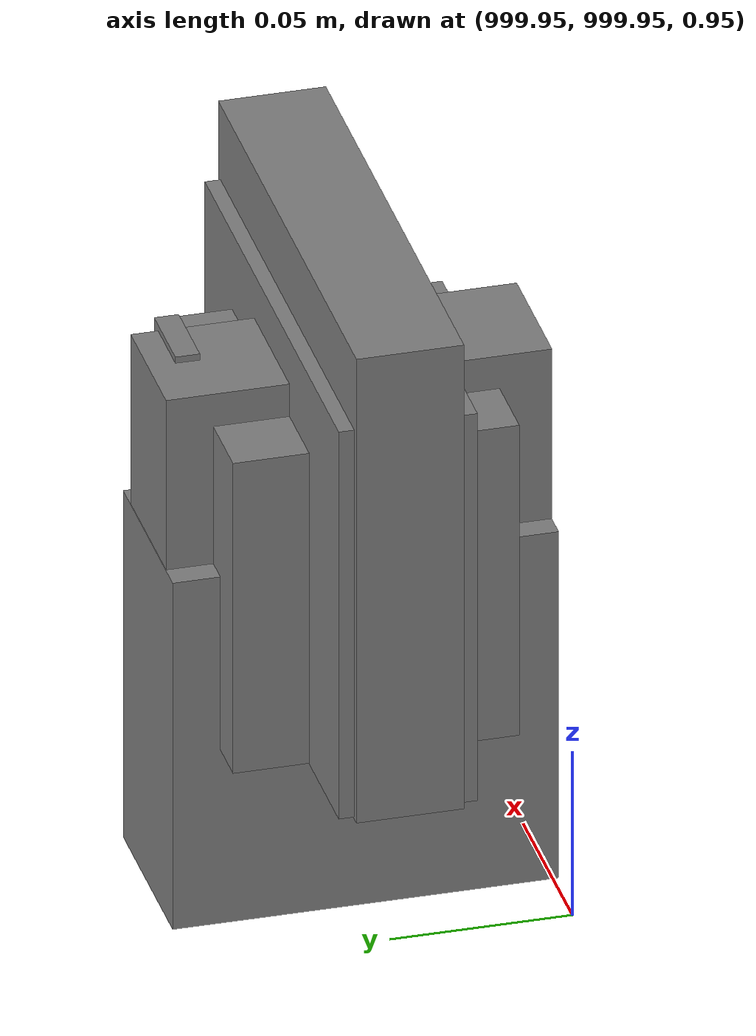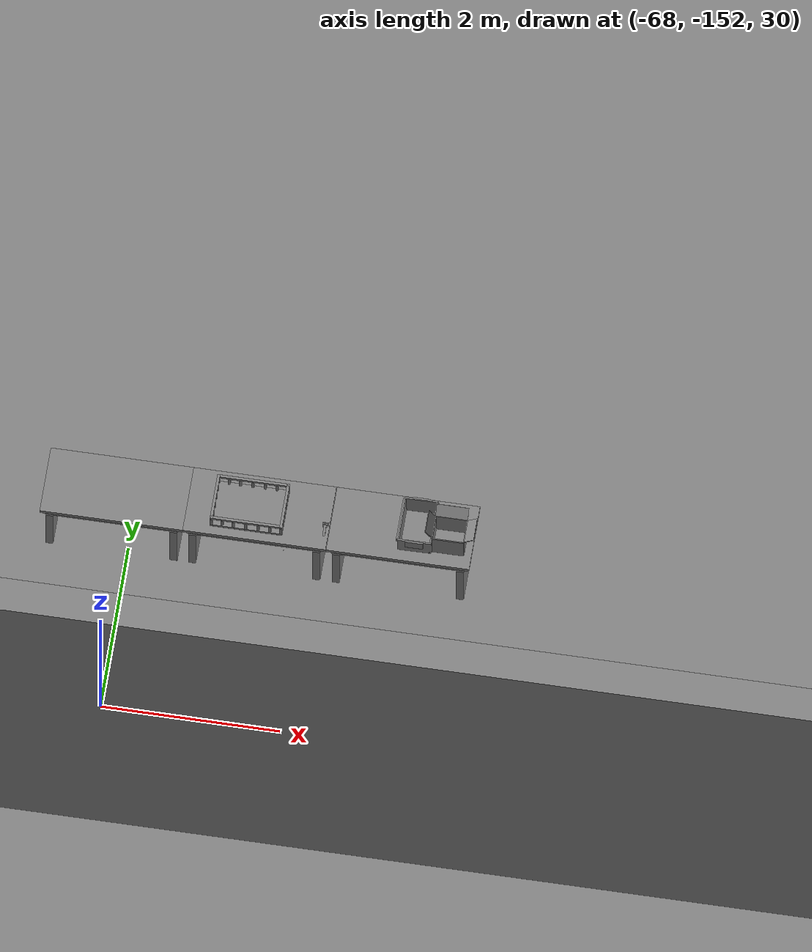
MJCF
<mujoco>
    <option gravity="0.000000000 0.000000000 -9.810000420" timestep="0.0049999999" integrator="implicitfast" density="1.225" viscosity="1.8000001e-05" noslip_iterations="10" iterations="100" sdf_iterations="50">
        <flag multiccd="disable"/>
    </option>
    <size memory="1000M"/>
    <compiler coordinate="local"/>
    <worldbody>
        <light cutoff="30" pos="0 1 1" dir="0 -1 -2"/>
        <light cutoff="30" pos="0 -1 1" dir="0 1 -2"/>
        <body pos="-65.852233887 -148.896850586 31.169460297" euler="-174.420349121 56.895973206 36.772949219" mocap="true" name="spotlight4_SpotLight"/>
        <body pos="1000.000000000 1000.000000000 1.000000000" euler="0.000000000 0.000000000 180.000000000" name="openloong_gripper_2f85_fix_base_usda_battery_01">
            <geom contype="1" conaffinity="1" density="1000" type="box" material="" rgba="0.500000000 0.500000000 0.500000000 1.000000000" solimp="0.899999976 0.949999988 0.001000000" friction="1.000000000 0.005000000 0.000100000" solref="0.020000000 1.000000000" margin="0" condim="3" group="0" pos="-0.011123657 -0.041940309 0.101691343" quat="1.000000000 0.000000000 0.000000000 0.000000000" size="0.010800000 0.003375000 0.004725000" name="openloong_gripper_2f85_fix_base_usda_geom_FE050364_5351_49E4_8048_C2208293CB09"/>
            <geom contype="1" conaffinity="1" density="1000" type="box" material="" rgba="0.500000000 0.500000000 0.500000000 1.000000000" solimp="0.899999976 0.949999988 0.001000000" friction="1.000000000 0.005000000 0.000100000" solref="0.020000000 1.000000000" margin="0" condim="3" group="0" pos="-0.010876465 -0.044247437 0.047066893" quat="0.998702705 -0.050920475 0.000000000 0.000000000" size="0.009450001 0.002700000 0.024975000" name="openloong_gripper_2f85_fix_base_usda_geom_55A32008_D626_4E9D_AEC4_C6905F8858F5"/>
            <geom contype="1" conaffinity="1" density="1000" type="box" material="" rgba="0.500000000 0.500000000 0.500000000 1.000000000" solimp="0.899999976 0.949999988 0.001000000" friction="1.000000000 0.005000000 0.000100000" solref="0.020000000 1.000000000" margin="0" condim="3" group="0" pos="-0.001235962 -0.000659180 0.047381196" quat="1.000000000 0.000000000 0.000000000 0.000000000" size="0.039420001 0.039150000 0.047250003" name="openloong_gripper_2f85_fix_base_usda_geom_1D92CB02_E060_4DDE_A843_020BEB527FC6"/>
            <geom contype="1" conaffinity="1" density="1000" type="box" material="" rgba="0.500000000 0.500000000 0.500000000 1.000000000" solimp="0.899999976 0.949999988 0.001000000" friction="1.000000000 0.005000000 0.000100000" solref="0.020000000 1.000000000" margin="0" condim="3" group="0" pos="-0.010876465 -0.039138794 0.009851727" quat="1.000000000 0.000000000 0.000000000 0.000000000" size="0.009450001 0.010800000 0.013500000" name="openloong_gripper_2f85_fix_base_usda_geom_0AA2FC0A_2E28_45D0_90F8_4ED97304C3A2"/>
            <geom contype="1" conaffinity="1" density="1000" type="box" material="" rgba="0.500000000 0.500000000 0.500000000 1.000000000" solimp="0.899999976 0.949999988 0.001000000" friction="1.000000000 0.005000000 0.000100000" solref="0.020000000 1.000000000" margin="0" condim="3" group="0" pos="-0.010876465 -0.041528322 0.071508206" quat="1.000000000 0.000000000 0.000000000 0.000000000" size="0.009450001 0.002700000 0.027000001" name="openloong_gripper_2f85_fix_base_usda_geom_3D5B363E_A7A9_44D2_9D7E_C743BE45CE6C"/>
            <freejoint name="openloong_gripper_2f85_fix_base_usda_battery_01_joint"/>
            <site size="0.005000000 0.005000000 0.005000000" rgba="0.500000000 0.500000000 0.500000000 1.000000000" pos="0.000000000 0.000000000 0.000000000" quat="0.999961913 0.008726500 0.000000000 0.000000000" group="0" type="sphere" name="openloong_gripper_2f85_fix_base_usda_battery_01site"/>
        </body>
        <body pos="1000.000000000 1000.000000000 1.000000000" euler="0.000000000 0.000000000 180.000000000" name="openloong_gripper_2f85_fix_base_usda_cpu_fan">
            <geom contype="1" conaffinity="1" density="1000" type="box" material="" rgba="0.500000000 0.500000000 0.500000000 1.000000000" solimp="0.899999976 0.949999988 0.001000000" friction="1.000000000 0.005000000 0.000100000" solref="0.020000000 1.000000000" margin="0" condim="3" group="0" pos="0.000000000 0.000000000 0.070034981" quat="0.000000000 0.000000000 0.000000000 1.000000000" size="0.070700005 0.014699999 0.070700005" name="openloong_gripper_2f85_fix_base_usda_geom_1D924B7E_6940_434A_8E32_ED84957588E3"/>
            <freejoint name="openloong_gripper_2f85_fix_base_usda_cpu_fan_joint"/>
            <site size="0.005000000 0.005000000 0.005000000" rgba="0.500000000 0.500000000 0.500000000 1.000000000" pos="0.000000000 0.000000000 0.000000000" quat="0.999961913 0.008726535 0.000000000 0.000000000" group="0" type="sphere" name="openloong_gripper_2f85_fix_base_usda_cpu_fancsite"/>
        </body>
        <body pos="1000.000000000 1000.000000000 1.000000000" euler="0.000000000 0.000000000 180.000000000" name="openloong_gripper_2f85_fix_base_usda_wifi_box">
            <geom contype="1" conaffinity="1" density="1000" type="box" material="" rgba="0.500000000 0.500000000 0.500000000 1.000000000" solimp="0.899999976 0.949999988 0.001000000" friction="1.000000000 0.005000000 0.000100000" solref="0.020000000 1.000000000" margin="0" condim="3" group="0" pos="0.000000000 0.000000000 0.058978677" quat="0.000000000 0.000000047 0.000000000 1.000000000" size="0.068499997 0.018999999 0.059000000" name="openloong_gripper_2f85_fix_base_usda_geom_33B0DEA2_82D8_452B_9976_C38C236A23F2"/>
            <freejoint name="openloong_gripper_2f85_fix_base_usda_wifi_box_joint"/>
            <site size="0.005000000 0.005000000 0.005000000" rgba="0.500000000 0.500000000 0.500000000 1.000000000" pos="0.000000000 0.000000000 0.000000000" quat="0.999961913 0.008726500 0.000000000 0.000000000" group="0" type="sphere" name="openloong_gripper_2f85_fix_base_usda_wifi_boxsite"/>
        </body>
        <body pos="-65.812263489 -149.634872437 31.170103073" euler="179.913116455 -14.584623337 -147.656600952" mocap="true" name="spotlight6_SpotLight"/>
        <body pos="1000.000000000 1000.000000000 1.000000000" euler="0.000011953 0.000005123 -179.999984741" name="openloong_gripper_2f85_fix_base_usda_intel_box">
            <geom contype="1" conaffinity="1" density="1000" type="box" material="" rgba="0.500000000 0.500000000 0.500000000 1.000000000" solimp="0.899999976 0.949999988 0.001000000" friction="1.000000000 0.005000000 0.000100000" solref="0.020000000 1.000000000" margin="0" condim="3" group="0" pos="0.000000000 -0.000067139 0.000082284" quat="0.707106709 0.000000225 0.000000253 0.707106650" size="0.052800003 0.025300000 0.052800003" name="openloong_gripper_2f85_fix_base_usda_geom_9DBAE16E_F3FE_41F8_A706_35FB166068B0"/>
            <freejoint name="openloong_gripper_2f85_fix_base_usda_intel_box_joint"/>
            <site size="0.005000000 0.005000000 0.005000000" rgba="0.500000000 0.500000000 0.500000000 1.000000000" pos="0.000000000 0.000000000 0.000000000" quat="0.999961913 0.008726500 0.000000000 0.000000000" group="0" type="sphere" name="openloong_gripper_2f85_fix_base_usda_intel_boxsite"/>
        </body>
        <body pos="1000.000000000 999.999938965 1.000000000" euler="0.000000000 0.000000000 180.000000000" name="openloong_gripper_2f85_fix_base_usda_intelcore_i5">
            <geom contype="1" conaffinity="1" density="1000" type="box" material="" rgba="0.500000000 0.500000000 0.500000000 1.000000000" solimp="0.899999976 0.949999988 0.001000000" friction="1.000000000 0.005000000 0.000100000" solref="0.020000000 1.000000000" margin="0" condim="3" group="0" pos="0.000000000 0.000000000 0.051722717" quat="0.707106709 0.000000000 0.000000000 -0.707106769" size="0.052800000 0.018080002 0.052800000" name="openloong_gripper_2f85_fix_base_usda_geom_098A503D_6488_4993_8F2A_C11DA5AD1829"/>
            <freejoint name="openloong_gripper_2f85_fix_base_usda_intelcore_i5_joint"/>
            <site size="0.005000000 0.005000000 0.005000000" rgba="0.500000000 0.500000000 0.500000000 1.000000000" pos="0.000000000 0.000000000 0.000000000" quat="0.999961913 0.008726534 0.000000000 0.000000000" group="0" type="sphere" name="openloong_gripper_2f85_fix_base_usda_intelcore_i5site"/>
        </body>
        <body pos="-65.857582092 -149.799423218 31.167972565" euler="-179.902648926 65.921638489 -156.649948120" mocap="true" name="spotlight2_SpotLight"/>
        <body pos="-64.866622925 -149.383972168 30.183746338" euler="89.999984741 89.999946594 0.000000000" name="openloong_gripper_2f85_fix_base_usda_bluebox_01">
            <geom contype="1" conaffinity="1" density="1000" type="box" material="" rgba="0.500000000 0.500000000 0.500000000 1.000000000" solimp="0.899999976 0.949999988 0.001000000" friction="1.000000000 0.005000000 0.000100000" solref="0.020000000 1.000000000" margin="0" condim="3" group="0" pos="0.276580811 0.187225342 0.000068665" quat="0.707106948 0.000077471 0.707106352 0.000077486" size="0.100000001 0.057999998 0.010000000" name="openloong_gripper_2f85_fix_base_usda_geom_41C161FC_9792_4482_8755_4E2BA599C7E0"/>
            <geom contype="1" conaffinity="1" density="1000" type="box" material="" rgba="0.500000000 0.500000000 0.500000000 1.000000000" solimp="0.899999976 0.949999988 0.001000000" friction="1.000000000 0.005000000 0.000100000" solref="0.020000000 1.000000000" margin="0" condim="3" group="0" pos="0.000000000 0.002883911 0.000000000" quat="0.999999881 0.000000000 0.000000000 0.000000000" size="0.254000008 0.003000000 0.172000006" name="openloong_gripper_2f85_fix_base_usda_geom_A00998BA_E51B_4B7B_93B5_B6236C75173E"/>
            <geom contype="1" conaffinity="1" density="1000" type="box" material="" rgba="0.500000000 0.500000000 0.500000000 1.000000000" solimp="0.899999976 0.949999988 0.001000000" friction="1.000000000 0.005000000 0.000100000" solref="0.020000000 1.000000000" margin="0" condim="3" group="0" pos="0.000000000 0.124874115 0.173484802" quat="0.999796331 0.020176515 -0.000000015 0.000000030" size="0.259999990 0.119999997 0.007000000" name="openloong_gripper_2f85_fix_base_usda_geom_4B1C40B0_AF7A_4E68_8A08_BE6C594A3071"/>
            <geom contype="1" conaffinity="1" density="1000" type="box" material="" rgba="0.500000000 0.500000000 0.500000000 1.000000000" solimp="0.899999976 0.949999988 0.001000000" friction="1.000000000 0.005000000 0.000100000" solref="0.020000000 1.000000000" margin="0" condim="3" group="0" pos="0.000000000 0.124874115 -0.173469543" quat="0.999796331 -0.020176545 -0.000000015 0.000000000" size="0.259999990 0.119999997 0.007000000" name="openloong_gripper_2f85_fix_base_usda_geom_B9EE371E_3C44_4DF9_BCD1_99F5590D6783"/>
            <geom contype="1" conaffinity="1" density="1000" type="box" material="" rgba="0.500000000 0.500000000 0.500000000 1.000000000" solimp="0.899999976 0.949999988 0.001000000" friction="1.000000000 0.005000000 0.000100000" solref="0.020000000 1.000000000" margin="0" condim="3" group="0" pos="0.000000000 0.214008331 0.188980103" quat="0.999912977 0.013176724 0.000000015 0.000000000" size="0.259999990 0.029999999 0.012500000" name="openloong_gripper_2f85_fix_base_usda_geom_72C2727A_BF64_4B2C_A51D_C6E0D8F65A4B"/>
            <geom contype="1" conaffinity="1" density="1000" type="box" material="" rgba="0.500000000 0.500000000 0.500000000 1.000000000" solimp="0.899999976 0.949999988 0.001000000" friction="1.000000000 0.005000000 0.000100000" solref="0.020000000 1.000000000" margin="0" condim="3" group="0" pos="-0.258361816 0.125289917 0.001876831" quat="0.702796936 -0.020792112 0.710783124 0.020769298" size="0.189999998 0.119999997 0.009000000" name="openloong_gripper_2f85_fix_base_usda_geom_2AB4A6BB_B257_4E16_A2EA_27AF401F45A1"/>
            <geom contype="1" conaffinity="1" density="1000" type="box" material="" rgba="0.500000000 0.500000000 0.500000000 1.000000000" solimp="0.899999976 0.949999988 0.001000000" friction="1.000000000 0.005000000 0.000100000" solref="0.020000000 1.000000000" margin="0" condim="3" group="0" pos="0.000000000 0.214008331 -0.188980103" quat="0.999912977 -0.013176769 0.000000030 0.000000015" size="0.259999990 0.029999999 0.012500000" name="openloong_gripper_2f85_fix_base_usda_geom_78344087_E8AB_425A_8C9D_65DA077098D1"/>
            <geom contype="1" conaffinity="1" density="1000" type="box" material="" rgba="0.500000000 0.500000000 0.500000000 1.000000000" solimp="0.899999976 0.949999988 0.001000000" friction="1.000000000 0.005000000 0.000100000" solref="0.020000000 1.000000000" margin="0" condim="3" group="0" pos="-0.276611328 0.187225342 0.000068665" quat="0.707106650 0.000077441 0.707106709 0.000077456" size="0.100000001 0.057999998 0.010000000" name="openloong_gripper_2f85_fix_base_usda_geom_BB52E4E4_D58F_4B5D_9C75_23CADB683CE9"/>
            <geom contype="1" conaffinity="1" density="1000" type="box" material="" rgba="0.500000000 0.500000000 0.500000000 1.000000000" solimp="0.899999976 0.949999988 0.001000000" friction="1.000000000 0.005000000 0.000100000" solref="0.020000000 1.000000000" margin="0" condim="3" group="0" pos="0.258331299 0.125289917 0.001876831" quat="0.702851415 0.018856421 0.710823774 -0.019329369" size="0.189999998 0.119999997 0.009000000" name="openloong_gripper_2f85_fix_base_usda_geom_0ACB9DDC_DB07_432E_86FD_0D305420D46F"/>
            <freejoint name="openloong_gripper_2f85_fix_base_usda_bluebox_01_joint"/>
            <site size="0.005000000 0.005000000 0.005000000" rgba="0.500000000 0.500000000 0.500000000 1.000000000" pos="0.000000000 0.000000000 0.000000000" quat="0.999961913 0.008726534 0.000000000 0.000000000" group="0" type="sphere" name="openloong_gripper_2f85_fix_base_usda_bluebox_01site"/>
        </body>
        <body pos="-64.496299744 -149.491867065 30.235729218" euler="0.000000000 0.000000000 89.999946594" name="openloong_gripper_2f85_fix_base_usda_cardboardbox_01">
            <geom contype="1" conaffinity="1" density="1000" type="box" material="" rgba="0.500000000 0.500000000 0.500000000 1.000000000" solimp="0.899999976 0.949999988 0.001000000" friction="1.000000000 0.005000000 0.000100000" solref="0.020000000 1.000000000" margin="0" condim="3" group="0" pos="-0.003166199 -0.004086494 0.005052090" quat="1.000000000 0.000000000 0.000000000 0.000000000" size="0.142499998 0.177500010 0.005000000" name="openloong_gripper_2f85_fix_base_usda_geom_D6454223_C356_42CA_A0BF_522907BDB6C2"/>
            <geom contype="1" conaffinity="1" density="1000" type="box" material="" rgba="0.500000000 0.500000000 0.500000000 1.000000000" solimp="0.899999976 0.949999988 0.001000000" friction="1.000000000 0.005000000 0.000100000" solref="0.020000000 1.000000000" margin="0" condim="3" group="0" pos="-0.003166199 0.170316696 0.150570869" quat="1.000000000 0.000000000 0.000000000 0.000000000" size="0.142499998 0.005000000 0.149999991" name="openloong_gripper_2f85_fix_base_usda_geom_15B40131_9AF9_4438_8699_83DA41241676"/>
            <geom contype="1" conaffinity="1" density="1000" type="box" material="" rgba="0.500000000 0.500000000 0.500000000 1.000000000" solimp="0.899999976 0.949999988 0.001000000" friction="1.000000000 0.005000000 0.000100000" solref="0.020000000 1.000000000" margin="0" condim="3" group="0" pos="-0.147399902 -0.005307198 0.150570869" quat="1.000000000 0.000000000 0.000000000 0.000000000" size="0.005000000 0.177500010 0.149999991" name="openloong_gripper_2f85_fix_base_usda_geom_C8D90FD8_8D47_430E_AEA1_FFE39EF4DA29"/>
            <geom contype="1" conaffinity="1" density="1000" type="box" material="" rgba="0.500000000 0.500000000 0.500000000 1.000000000" solimp="0.899999976 0.949999988 0.001000000" friction="1.000000000 0.005000000 0.000100000" solref="0.020000000 1.000000000" margin="0" condim="3" group="0" pos="0.140275955 -0.005307198 0.150570869" quat="1.000000000 0.000000000 0.000000000 0.000000000" size="0.005000000 0.177500010 0.149999991" name="openloong_gripper_2f85_fix_base_usda_geom_500FB019_12F8_467E_BD30_68833DB85F15"/>
            <geom contype="1" conaffinity="1" density="1000" type="box" material="" rgba="0.500000000 0.500000000 0.500000000 1.000000000" solimp="0.899999976 0.949999988 0.001000000" friction="1.000000000 0.005000000 0.000100000" solref="0.020000000 1.000000000" margin="0" condim="3" group="0" pos="-0.003166199 -0.181550980 0.150570869" quat="1.000000000 0.000000000 0.000000000 0.000000000" size="0.142499998 0.005000000 0.149999991" name="openloong_gripper_2f85_fix_base_usda_geom_9AA66F2A_ABC6_447C_BB81_FB0F43BC8711"/>
            <freejoint name="openloong_gripper_2f85_fix_base_usda_cardboardbox_01_joint"/>
            <site size="0.005000000 0.005000000 0.005000000" rgba="0.500000000 0.500000000 0.500000000 1.000000000" pos="0.000000000 0.000000000 0.000000000" quat="0.999961913 0.008726535 0.000000000 0.000000000" group="0" type="sphere" name="openloong_gripper_2f85_fix_base_usda_site_89B0D81F_40DC_408C_A34C_B68B2A0A6359"/>
            <body pos="0.139160156 -0.004048347 0.301930904" euler="-179.999954224 49.383502960 179.999954224" name="openloong_gripper_2f85_fix_base_usda_A1_006">
                <geom contype="1" conaffinity="1" density="1000" type="box" material="" rgba="0.500000000 0.500000000 0.500000000 1.000000000" solimp="0.899999976 0.949999988 0.001000000" friction="1.000000000 0.005000000 0.000100000" solref="0.020000000 1.000000000" margin="0" condim="3" group="0" pos="-0.071587563 0.000009537 0.001745224" quat="0.999999881 0.000000000 0.000000000 0.000000000" size="0.071249999 0.179999992 0.002500000" name="openloong_gripper_2f85_fix_base_usda_geom_A02C207E_607F_4FCC_BB4F_26E34FD0112D"/>
                <joint armature="0" stiffness="0.07" damping="0.0099999998" axis="0.000000 1.000000 0.000000" type="hinge" name="openloong_gripper_2f85_fix_base_usda_A1_006"/>
            </body>
            <body pos="-0.145902634 -0.004086494 0.301938057" euler="-180.000000000 -60.000011444 -180.000000000" name="openloong_gripper_2f85_fix_base_usda_A2_006">
                <geom contype="1" conaffinity="1" density="1000" type="box" material="" rgba="0.500000000 0.500000000 0.500000000 1.000000000" solimp="0.899999976 0.949999988 0.001000000" friction="1.000000000 0.005000000 0.000100000" solref="0.020000000 1.000000000" margin="0" condim="3" group="0" pos="0.071268082 0.000009537 0.002717972" quat="0.000002921 0.000000000 -0.000000030 0.999999881" size="0.071249999 0.179999992 0.002500000" name="openloong_gripper_2f85_fix_base_usda_geom_3ADF5EDC_356F_4AB1_90AA_AE31D860D58C"/>
                <joint armature="0" stiffness="0.07" damping="0.0099999998" axis="0.000000 1.000000 0.000000" type="hinge" name="openloong_gripper_2f85_fix_base_usda_A2_006"/>
            </body>
            <body pos="-0.003385544 0.175991058 0.301930904" euler="-125.858116150 -0.000004561 0.000002331" name="openloong_gripper_2f85_fix_base_usda_B2_006">
                <geom contype="1" conaffinity="1" density="1000" type="box" material="" rgba="0.500000000 0.500000000 0.500000000 1.000000000" solimp="0.899999976 0.949999988 0.001000000" friction="1.000000000 0.005000000 0.000100000" solref="0.020000000 1.000000000" margin="0" condim="3" group="0" pos="0.000009537 -0.070939064 -0.002470016" quat="0.999614120 0.027776197 -0.000000015 0.000000030" size="0.137500003 0.064999998 0.005000000" name="openloong_gripper_2f85_fix_base_usda_geom_17DDCEAE_E18A_4FBA_9CBA_B18DDDBDCAEE"/>
                <joint armature="0" stiffness="0.07" damping="0.0099999998" axis="1.000000 0.000000 0.000000" type="hinge" name="openloong_gripper_2f85_fix_base_usda_B2_006"/>
            </body>
            <body pos="-0.003385544 -0.184140205 0.301938057" euler="147.805557251 0.000000000 0.000000000" name="openloong_gripper_2f85_fix_base_usda_B1_006">
                <geom contype="1" conaffinity="1" density="1000" type="box" material="" rgba="0.500000000 0.500000000 0.500000000 1.000000000" solimp="0.899999976 0.949999988 0.001000000" friction="1.000000000 0.005000000 0.000100000" solref="0.020000000 1.000000000" margin="0" condim="3" group="0" pos="-0.000028610 0.070202351 -0.002703667" quat="0.999614179 -0.027776167 0.000000000 0.000000000" size="0.137500003 0.064999998 0.005000000" name="openloong_gripper_2f85_fix_base_usda_geom_D0A40716_A4DF_4719_938B_8E006AA572DB"/>
                <joint armature="0" stiffness="0.07" damping="0.0099999998" axis="1.000000 0.000000 0.000000" type="hinge" name="openloong_gripper_2f85_fix_base_usda_B1_006"/>
            </body>
        </body>
        <body pos="-65.882858276 -149.481979370 30.229999542" euler="-64.487716675 0.000000000 0.000000000" name="openloong_gripper_2f85_fix_base_usda_Barcode">
            <geom contype="1" conaffinity="1" density="1000" type="box" material="" rgba="0.500000000 0.500000000 0.500000000 1.000000000" solimp="0.899999976 0.949999988 0.001000000" friction="1.000000000 0.005000000 0.000100000" solref="0.020000000 1.000000000" margin="0" condim="3" group="0" pos="0.000000000 0.013038635 0.001419067" quat="0.000000000 0.000000000 0.000000000 1.000000119" size="0.034000002 0.010000000 0.017999999" name="openloong_gripper_2f85_fix_base_usda_geom_7C8C169B_36C3_4D0E_833E_C8F3233A0DC2"/>
            <geom contype="1" conaffinity="1" density="1000" type="box" material="" rgba="0.500000000 0.500000000 0.500000000 1.000000000" solimp="0.899999976 0.949999988 0.001000000" friction="1.000000000 0.005000000 0.000100000" solref="0.020000000 1.000000000" margin="0" condim="3" group="0" pos="0.000000000 -0.035301208 -0.007095337" quat="0.000000000 0.000000000 -0.043619365 0.999048233" size="0.028999999 0.010000000 0.020000000" name="openloong_gripper_2f85_fix_base_usda_geom_C3D4878D_80A8_4B22_89B9_9D4F5367746D"/>
            <geom contype="1" conaffinity="1" density="1000" type="box" material="" rgba="0.500000000 0.500000000 0.500000000 1.000000000" solimp="0.899999976 0.949999988 0.001000000" friction="1.000000000 0.005000000 0.000100000" solref="0.020000000 1.000000000" margin="0" condim="3" group="0" pos="0.000000000 -0.043411255 -0.011749268" quat="0.922262907 0.386563420 0.000000000 0.000000000" size="0.026000001 0.010000000 0.020000000" name="openloong_gripper_2f85_fix_base_usda_geom_A19F8EB3_08DA_49A2_B927_A634816A43D4"/>
            <geom contype="1" conaffinity="1" density="1000" type="box" material="" rgba="0.500000000 0.500000000 0.500000000 1.000000000" solimp="0.899999976 0.949999988 0.001000000" friction="1.000000000 0.005000000 0.000100000" solref="0.020000000 1.000000000" margin="0" condim="3" group="0" pos="0.000000000 -0.016967773 -0.031860352" quat="0.000000000 0.000000000 0.000000000 1.000000119" size="0.008000000 0.010000000 0.013000000" name="openloong_gripper_2f85_fix_base_usda_geom_496B2CE8_76BB_4DC2_8147_E9AEAF009145"/>
            <geom contype="1" conaffinity="1" density="1000" type="box" material="" rgba="0.500000000 0.500000000 0.500000000 1.000000000" solimp="0.899999976 0.949999988 0.001000000" friction="1.000000000 0.005000000 0.000100000" solref="0.020000000 1.000000000" margin="0" condim="3" group="0" pos="0.000000000 -0.001869202 0.000312805" quat="0.953716993 0.300705761 0.000000000 0.000000000" size="0.032000002 0.010000000 0.018999999" name="openloong_gripper_2f85_fix_base_usda_geom_9F8369BD_AE67_47A8_9F8B_51B3C40D21D1"/>
            <geom contype="1" conaffinity="1" density="1000" type="box" material="" rgba="0.500000000 0.500000000 0.500000000 1.000000000" solimp="0.899999976 0.949999988 0.001000000" friction="1.000000000 0.005000000 0.000100000" solref="0.020000000 1.000000000" margin="0" condim="3" group="0" pos="0.000000000 -0.019531250 -0.003173828" quat="0.953716993 0.300705761 0.000000000 0.000000000" size="0.030999999 0.010000000 0.020000000" name="openloong_gripper_2f85_fix_base_usda_geom_E96BD3C4_82F6_45BB_A296_9A9C0C8CAB93"/>
            <geom contype="1" conaffinity="1" density="1000" type="box" material="" rgba="0.500000000 0.500000000 0.500000000 1.000000000" solimp="0.899999976 0.949999988 0.001000000" friction="1.000000000 0.005000000 0.000100000" solref="0.020000000 1.000000000" margin="0" condim="3" group="0" pos="0.000000000 -0.035301208 -0.007095337" quat="0.953716993 0.300705761 0.000000000 0.000000000" size="0.028999999 0.010000000 0.020000000" name="openloong_gripper_2f85_fix_base_usda_geom_E88B2048_349D_4F2E_90B7_9060F9EF7161"/>
            <geom contype="1" conaffinity="1" density="1000" type="box" material="" rgba="0.500000000 0.500000000 0.500000000 1.000000000" solimp="0.899999976 0.949999988 0.001000000" friction="1.000000000 0.005000000 0.000100000" solref="0.020000000 1.000000000" margin="0" condim="3" group="0" pos="0.000000000 -0.042617798 -0.071121216" quat="0.000000000 0.000000000 0.000000000 1.000000119" size="0.013000000 0.021000000 0.059999999" name="openloong_gripper_2f85_fix_base_usda_geom_26FD41A5_6F2C_4DE4_AE7D_CD41C39C4775"/>
            <freejoint name="openloong_gripper_2f85_fix_base_usda_Barcode_joint"/>
            <site size="0.005000000 0.005000000 0.005000000" rgba="0.500000000 0.500000000 0.500000000 1.000000000" pos="0.000000000 0.000000000 0.000000000" quat="1.000000000 0.000000000 0.000000000 0.000000000" group="0" type="sphere" name="openloong_gripper_2f85_fix_base_usda_Barcode_site"/>
        </body>
        <body pos="-66.745018005 -149.392349243 30.184000015" euler="0.000000000 0.000000000 89.999946594" name="[22330416246891]_Basket_01">
            <geom contype="1" conaffinity="1" density="1000" type="box" material="" rgba="0.500000000 0.500000000 0.500000000 1.000000000" solimp="0.899999976 0.949999988 0.001000000" friction="1.000000000 0.005000000 0.000100000" solref="0.020000000 1.000000000" margin="0" condim="3" group="0" pos="-0.052425385 0.389207840 0.089787483" quat="0.707107008 0.000000000 0.000000000 0.707106411" size="0.014249999 0.014249999 0.059999999" name="[22330416246891]_geom_E773657F_F63C_47C6_B70D_08BDB65147F4"/>
            <geom contype="1" conaffinity="1" density="1000" type="box" material="" rgba="0.500000000 0.500000000 0.500000000 1.000000000" solimp="0.899999976 0.949999988 0.001000000" friction="1.000000000 0.005000000 0.000100000" solref="0.020000000 1.000000000" margin="0" condim="3" group="0" pos="0.264015198 -0.133043289 0.089787483" quat="0.707107008 0.000000000 0.000000000 0.707106411" size="0.014249999 0.014249999 0.059999999" name="[22330416246891]_geom_8B1150E2_294C_4E2D_9269_3A1DD20AE4C2"/>
            <geom contype="1" conaffinity="1" density="1000" type="box" material="" rgba="0.500000000 0.500000000 0.500000000 1.000000000" solimp="0.899999976 0.949999988 0.001000000" friction="1.000000000 0.005000000 0.000100000" solref="0.020000000 1.000000000" margin="0" condim="3" group="0" pos="-0.264015198 -0.265548706 0.089793205" quat="0.707107008 0.000000000 0.000000000 0.707106411" size="0.014249999 0.014249999 0.059999999" name="[22330416246891]_geom_C9C3FA4C_BDA5_4115_8EB7_562FB53781B4"/>
            <geom contype="1" conaffinity="1" density="1000" type="box" material="" rgba="0.500000000 0.500000000 0.500000000 1.000000000" solimp="0.899999976 0.949999988 0.001000000" friction="1.000000000 0.005000000 0.000100000" solref="0.020000000 1.000000000" margin="0" condim="3" group="0" pos="-0.160263062 -0.389322281 0.089793205" quat="0.707107008 0.000000000 0.000000000 0.707106411" size="0.014249999 0.014249999 0.059999999" name="[22330416246891]_geom_AF21BC9E_AC44_4B37_A14C_ECEE9E147DF2"/>
            <geom contype="1" conaffinity="1" density="1000" type="box" material="" rgba="0.500000000 0.500000000 0.500000000 1.000000000" solimp="0.899999976 0.949999988 0.001000000" friction="1.000000000 0.005000000 0.000100000" solref="0.020000000 1.000000000" margin="0" condim="3" group="0" pos="0.162265778 -0.389322281 0.089787483" quat="0.707107008 0.000000000 0.000000000 0.707106411" size="0.014249999 0.014249999 0.059999999" name="[22330416246891]_geom_1BAC40C4_8032_47EB_BD9E_7859BAD748CD"/>
            <geom contype="1" conaffinity="1" density="1000" type="box" material="" rgba="0.500000000 0.500000000 0.500000000 1.000000000" solimp="0.899999976 0.949999988 0.001000000" friction="1.000000000 0.005000000 0.000100000" solref="0.020000000 1.000000000" margin="0" condim="3" group="0" pos="0.264015198 0.389207840 0.089787483" quat="0.707107008 0.000000000 0.000000000 0.707106411" size="0.014249999 0.014249999 0.059999999" name="[22330416246891]_geom_0C036C61_F737_41BB_8942_394B0ECEAD08"/>
            <geom contype="1" conaffinity="1" density="1000" type="box" material="" rgba="0.500000000 0.500000000 0.500000000 1.000000000" solimp="0.899999976 0.949999988 0.001000000" friction="1.000000000 0.005000000 0.000100000" solref="0.020000000 1.000000000" margin="0" condim="3" group="0" pos="-0.264015198 -0.133043289 0.089793205" quat="0.707107008 0.000000000 0.000000000 0.707106411" size="0.014249999 0.014249999 0.059999999" name="[22330416246891]_geom_A1A9E313_FEDB_4C2E_8D6C_C28718784371"/>
            <geom contype="1" conaffinity="1" density="1000" type="box" material="" rgba="0.500000000 0.500000000 0.500000000 1.000000000" solimp="0.899999976 0.949999988 0.001000000" friction="1.000000000 0.005000000 0.000100000" solref="0.020000000 1.000000000" margin="0" condim="3" group="0" pos="-0.264026642 0.269256592 0.089793205" quat="0.707107008 0.000000000 0.000000000 0.707106411" size="0.014249999 0.014249999 0.059999999" name="[22330416246891]_geom_3EAE07AC_6F88_4698_BB5B_98AC2B120D8E"/>
            <geom contype="1" conaffinity="1" density="1000" type="box" material="" rgba="0.500000000 0.500000000 0.500000000 1.000000000" solimp="0.899999976 0.949999988 0.001000000" friction="1.000000000 0.005000000 0.000100000" solref="0.020000000 1.000000000" margin="0" condim="3" group="0" pos="0.054462433 0.389207840 0.089787483" quat="0.707107008 0.000000000 0.000000000 0.707106411" size="0.014249999 0.014249999 0.059999999" name="[22330416246891]_geom_E6C4C592_F5A5_43DE_9291_C0E9D366C736"/>
            <geom contype="1" conaffinity="1" density="1000" type="box" material="" rgba="0.500000000 0.500000000 0.500000000 1.000000000" solimp="0.899999976 0.949999988 0.001000000" friction="1.000000000 0.005000000 0.000100000" solref="0.020000000 1.000000000" margin="0" condim="3" group="0" pos="0.054462433 -0.389322281 0.089787483" quat="0.707107008 0.000000000 0.000000000 0.707106411" size="0.014249999 0.014249999 0.059999999" name="[22330416246891]_geom_8AD59AFF_B4BD_4508_BEDE_C446585083C7"/>
            <geom contype="1" conaffinity="1" density="1000" type="box" material="" rgba="0.500000000 0.500000000 0.500000000 1.000000000" solimp="0.899999976 0.949999988 0.001000000" friction="1.000000000 0.005000000 0.000100000" solref="0.020000000 1.000000000" margin="0" condim="3" group="0" pos="0.264015198 0.269256592 0.089793205" quat="0.707107008 0.000000000 0.000000000 0.707106411" size="0.014249999 0.014249999 0.059999999" name="[22330416246891]_geom_709B37C8_EA57_4E8B_AD9C_BE6ABCDC16EB"/>
            <geom contype="1" conaffinity="1" density="1000" type="box" material="" rgba="0.500000000 0.500000000 0.500000000 1.000000000" solimp="0.899999976 0.949999988 0.001000000" friction="1.000000000 0.005000000 0.000100000" solref="0.020000000 1.000000000" margin="0" condim="3" group="0" pos="0.264015198 -0.389322281 0.089787483" quat="0.707107008 0.000000000 0.000000000 0.707106411" size="0.014249999 0.014249999 0.059999999" name="[22330416246891]_geom_17625AD7_7903_45D2_BEAF_BCE384E90C6E"/>
            <geom contype="1" conaffinity="1" density="1000" type="box" material="" rgba="0.500000000 0.500000000 0.500000000 1.000000000" solimp="0.899999976 0.949999988 0.001000000" friction="1.000000000 0.005000000 0.000100000" solref="0.020000000 1.000000000" margin="0" condim="3" group="0" pos="0.000000000 0.000000000 0.015998840" quat="0.707107008 0.000000000 0.000000000 0.707106411" size="0.403499991 0.279000014 0.015750000" name="[22330416246891]_geom_A133D475_72C1_4794_93F7_C09637FFD694"/>
            <geom contype="1" conaffinity="1" density="1000" type="box" material="" rgba="0.500000000 0.500000000 0.500000000 1.000000000" solimp="0.899999976 0.949999988 0.001000000" friction="1.000000000 0.005000000 0.000100000" solref="0.020000000 1.000000000" margin="0" condim="3" group="0" pos="0.000000000 -0.389476776 0.163619041" quat="0.707107008 0.000000000 0.000000000 0.707106411" size="0.015000000 0.277500004 0.015750000" name="[22330416246891]_geom_D3F99392_4FE7_4C54_9E25_504EA35DEA40"/>
            <geom contype="1" conaffinity="1" density="1000" type="box" material="" rgba="0.500000000 0.500000000 0.500000000 1.000000000" solimp="0.899999976 0.949999988 0.001000000" friction="1.000000000 0.005000000 0.000100000" solref="0.020000000 1.000000000" margin="0" condim="3" group="0" pos="0.162265778 0.389207840 0.089787483" quat="0.707107008 0.000000000 0.000000000 0.707106411" size="0.014249999 0.014249999 0.059999999" name="[22330416246891]_geom_846A0A2A_CA14_4051_ACE7_6AD53EDCEAEE"/>
            <geom contype="1" conaffinity="1" density="1000" type="box" material="" rgba="0.500000000 0.500000000 0.500000000 1.000000000" solimp="0.899999976 0.949999988 0.001000000" friction="1.000000000 0.005000000 0.000100000" solref="0.020000000 1.000000000" margin="0" condim="3" group="0" pos="0.000000000 0.389471054 0.163619041" quat="0.707107008 0.000000000 0.000000000 0.707106411" size="0.015000000 0.277500004 0.015750000" name="[22330416246891]_geom_477FA2C4_6552_4E81_8F14_2EB70DC57CF4"/>
            <geom contype="1" conaffinity="1" density="1000" type="box" material="" rgba="0.500000000 0.500000000 0.500000000 1.000000000" solimp="0.899999976 0.949999988 0.001000000" friction="1.000000000 0.005000000 0.000100000" solref="0.020000000 1.000000000" margin="0" condim="3" group="0" pos="-0.263511658 0.000000000 0.163619041" quat="0.707107008 0.000000000 0.000000000 0.707106411" size="0.403499991 0.015000000 0.015750000" name="[22330416246891]_geom_BE430045_80B1_4CDE_9228_60820721C991"/>
            <geom contype="1" conaffinity="1" density="1000" type="box" material="" rgba="0.500000000 0.500000000 0.500000000 1.000000000" solimp="0.899999976 0.949999988 0.001000000" friction="1.000000000 0.005000000 0.000100000" solref="0.020000000 1.000000000" margin="0" condim="3" group="0" pos="-0.264015198 0.141334534 0.089793205" quat="0.707107008 0.000000000 0.000000000 0.707106411" size="0.014249999 0.014249999 0.059999999" name="[22330416246891]_geom_CAF074D2_B234_463C_B66B_0C4314826438"/>
            <geom contype="1" conaffinity="1" density="1000" type="box" material="" rgba="0.500000000 0.500000000 0.500000000 1.000000000" solimp="0.899999976 0.949999988 0.001000000" friction="1.000000000 0.005000000 0.000100000" solref="0.020000000 1.000000000" margin="0" condim="3" group="0" pos="0.264015198 -0.265548706 0.089787483" quat="0.707107008 0.000000000 0.000000000 0.707106411" size="0.014249999 0.014249999 0.059999999" name="[22330416246891]_geom_B26B5488_62DC_4193_BF89_E4CF4D6EA441"/>
            <geom contype="1" conaffinity="1" density="1000" type="box" material="" rgba="0.500000000 0.500000000 0.500000000 1.000000000" solimp="0.899999976 0.949999988 0.001000000" friction="1.000000000 0.005000000 0.000100000" solref="0.020000000 1.000000000" margin="0" condim="3" group="0" pos="-0.160263062 0.389207840 0.089787483" quat="0.707107008 0.000000000 0.000000000 0.707106411" size="0.014249999 0.014249999 0.059999999" name="[22330416246891]_geom_D19BE90A_6683_4B8F_A9AC_0FC8B4359E4E"/>
            <geom contype="1" conaffinity="1" density="1000" type="box" material="" rgba="0.500000000 0.500000000 0.500000000 1.000000000" solimp="0.899999976 0.949999988 0.001000000" friction="1.000000000 0.005000000 0.000100000" solref="0.020000000 1.000000000" margin="0" condim="3" group="0" pos="-0.052425385 -0.389322281 0.089787483" quat="0.707107008 0.000000000 0.000000000 0.707106411" size="0.014249999 0.014249999 0.059999999" name="[22330416246891]_geom_2A737325_BDF0_4B74_821C_D600A72BADF6"/>
            <geom contype="1" conaffinity="1" density="1000" type="box" material="" rgba="0.500000000 0.500000000 0.500000000 1.000000000" solimp="0.899999976 0.949999988 0.001000000" friction="1.000000000 0.005000000 0.000100000" solref="0.020000000 1.000000000" margin="0" condim="3" group="0" pos="-0.264026642 -0.389322281 0.089793205" quat="0.707107008 0.000000000 0.000000000 0.707106411" size="0.014249999 0.014249999 0.059999999" name="[22330416246891]_geom_9D9DE288_01B8_442E_99EF_86932BEE7F73"/>
            <geom contype="1" conaffinity="1" density="1000" type="box" material="" rgba="0.500000000 0.500000000 0.500000000 1.000000000" solimp="0.899999976 0.949999988 0.001000000" friction="1.000000000 0.005000000 0.000100000" solref="0.020000000 1.000000000" margin="0" condim="3" group="0" pos="0.264015198 0.141334534 0.089787483" quat="0.707107008 0.000000000 0.000000000 0.707106411" size="0.014249999 0.014249999 0.059999999" name="[22330416246891]_geom_630C42CC_AAD6_4F23_AEEE_C20E68129058"/>
            <geom contype="1" conaffinity="1" density="1000" type="box" material="" rgba="0.500000000 0.500000000 0.500000000 1.000000000" solimp="0.899999976 0.949999988 0.001000000" friction="1.000000000 0.005000000 0.000100000" solref="0.020000000 1.000000000" margin="0" condim="3" group="0" pos="-0.264015198 0.389207840 0.089793205" quat="0.707107008 0.000000000 0.000000000 0.707106411" size="0.014249999 0.014249999 0.059999999" name="[22330416246891]_geom_1A63BDE7_78D7_472B_9C3C_30379F53CFF5"/>
            <geom contype="1" conaffinity="1" density="1000" type="box" material="" rgba="0.500000000 0.500000000 0.500000000 1.000000000" solimp="0.899999976 0.949999988 0.001000000" friction="1.000000000 0.005000000 0.000100000" solref="0.020000000 1.000000000" margin="0" condim="3" group="0" pos="0.264015198 0.004480362 0.089787483" quat="0.707107008 0.000000000 0.000000000 0.707106411" size="0.014249999 0.014249999 0.059999999" name="[22330416246891]_geom_8C7DB133_D1F7_44AA_9C8B_004A20AD5DA5"/>
            <geom contype="1" conaffinity="1" density="1000" type="box" material="" rgba="0.500000000 0.500000000 0.500000000 1.000000000" solimp="0.899999976 0.949999988 0.001000000" friction="1.000000000 0.005000000 0.000100000" solref="0.020000000 1.000000000" margin="0" condim="3" group="0" pos="0.263694763 -0.000011444 0.163619041" quat="0.707107008 0.000000000 0.000000000 0.707106411" size="0.403499991 0.015000000 0.015750000" name="[22330416246891]_geom_CDF553D7_4DD9_4544_A11E_C188162B5A06"/>
            <geom contype="1" conaffinity="1" density="1000" type="box" material="" rgba="0.500000000 0.500000000 0.500000000 1.000000000" solimp="0.899999976 0.949999988 0.001000000" friction="1.000000000 0.005000000 0.000100000" solref="0.020000000 1.000000000" margin="0" condim="3" group="0" pos="-0.264015198 0.004480362 0.089793205" quat="0.707107008 0.000000000 0.000000000 0.707106411" size="0.014249999 0.014249999 0.059999999" name="[22330416246891]_geom_038DA1AF_6472_4ADE_A518_4E9C66790AE1"/>
            <freejoint name="[22330416246891]_joint_5DD18816_426E_4568_A17A_000B9BA6D14F"/>
        </body>
        <body pos="0.000000000 0.000000000 0.000000000" euler="0.000000000 0.000000000 0.000000000" name="Static Objects_Static Objects">
            <geom contype="1" conaffinity="1" density="1000" type="box" material="" rgba="0.500000000 0.500000000 0.500000000 1.000000000" solimp="0.899999976 0.949999988 0.001000000" friction="1.000000000 0.005000000 0.000100000" solref="0.020000000 1.000000000" margin="0" condim="3" group="0" pos="-67.544113159 -149.365814209 29.727830887" quat="0.500000417 0.499999970 0.499999553 0.499999970" size="0.381000012 0.319999993 0.041000001" name="Static Objects_geom_86B780A4_3B24_46D9_8050_8ADB7A51795B"/>
            <geom contype="1" conaffinity="1" density="1000" type="box" material="" rgba="0.500000000 0.500000000 0.500000000 1.000000000" solimp="0.899999976 0.949999988 0.001000000" friction="1.000000000 0.005000000 0.000100000" solref="0.020000000 1.000000000" margin="0" condim="3" group="0" pos="-68.239501953 -149.365814209 30.086868286" quat="0.500000417 0.499999970 0.499999553 0.499999970" size="0.370999992 0.039500002 0.745000005" name="Static Objects_geom_371ED124_3F61_4C1A_8A5D_7B36838E6796"/>
            <geom contype="1" conaffinity="1" density="1000" type="box" material="" rgba="0.500000000 0.500000000 0.500000000 1.000000000" solimp="0.899999976 0.949999988 0.001000000" friction="1.000000000 0.005000000 0.000100000" solref="0.020000000 1.000000000" margin="0" condim="3" group="0" pos="-68.239501953 -149.365814209 30.147235870" quat="0.500000417 0.499999970 0.499999553 0.499999970" size="0.400000006 0.022000000 0.800000012" name="Static Objects_geom_983DFBA2_A6B7_4EB8_81BB_5C60F7EA7ACC"/>
            <geom contype="1" conaffinity="1" density="1000" type="box" material="" rgba="0.500000000 0.500000000 0.500000000 1.000000000" solimp="0.899999976 0.949999988 0.001000000" friction="1.000000000 0.005000000 0.000100000" solref="0.020000000 1.000000000" margin="0" condim="3" group="0" pos="-68.934890747 -149.365814209 29.727830887" quat="0.500000417 0.499999970 0.499999553 0.499999970" size="0.381000012 0.319999993 0.041000001" name="Static Objects_geom_DB0BC434_9991_4870_98BB_0D4019ECB850"/>
            <geom contype="1" conaffinity="1" density="1000" type="box" material="" rgba="0.500000000 0.500000000 0.500000000 1.000000000" solimp="0.899999976 0.949999988 0.001000000" friction="1.000000000 0.005000000 0.000100000" solref="0.020000000 1.000000000" margin="0" condim="3" group="0" pos="-68.239501953 -149.365814209 29.561563492" quat="0.500000417 0.499999970 0.499999553 0.499999970" size="0.020000000 0.022000000 0.660000026" name="Static Objects_geom_2B4A85C7_6743_43AA_B5DC_36D7EED2CFE0"/>
            <geom contype="1" conaffinity="1" density="1000" type="box" material="" rgba="0.500000000 0.500000000 0.500000000 1.000000000" solimp="0.899999976 0.949999988 0.001000000" friction="1.000000000 0.005000000 0.000100000" solref="0.020000000 1.000000000" margin="0" condim="3" group="0" pos="-65.945671082 -149.365814209 29.727830887" quat="0.500000417 0.499999970 0.499999553 0.499999970" size="0.381000012 0.319999993 0.041000001" name="Static Objects_geom_B34E6CC4_0A9E_4F57_90CF_386C0E0E1AA7"/>
            <geom contype="1" conaffinity="1" density="1000" type="box" material="" rgba="0.500000000 0.500000000 0.500000000 1.000000000" solimp="0.899999976 0.949999988 0.001000000" friction="1.000000000 0.005000000 0.000100000" solref="0.020000000 1.000000000" margin="0" condim="3" group="0" pos="-66.641059875 -149.365814209 30.086868286" quat="0.500000417 0.499999970 0.499999553 0.499999970" size="0.370999992 0.039500002 0.745000005" name="Static Objects_geom_00AF5C2D_BFA6_434A_BB6F_1CA15CE77852"/>
            <geom contype="1" conaffinity="1" density="1000" type="box" material="" rgba="0.500000000 0.500000000 0.500000000 1.000000000" solimp="0.899999976 0.949999988 0.001000000" friction="1.000000000 0.005000000 0.000100000" solref="0.020000000 1.000000000" margin="0" condim="3" group="0" pos="-66.641059875 -149.365814209 30.147235870" quat="0.500000417 0.499999970 0.499999553 0.499999970" size="0.400000006 0.022000000 0.800000012" name="Static Objects_geom_1892AB21_5546_42BD_B1C2_124FC8EC277A"/>
            <geom contype="1" conaffinity="1" density="1000" type="box" material="" rgba="0.500000000 0.500000000 0.500000000 1.000000000" solimp="0.899999976 0.949999988 0.001000000" friction="1.000000000 0.005000000 0.000100000" solref="0.020000000 1.000000000" margin="0" condim="3" group="0" pos="-67.336448669 -149.365814209 29.727830887" quat="0.500000417 0.499999970 0.499999553 0.499999970" size="0.381000012 0.319999993 0.041000001" name="Static Objects_geom_EFDEE281_82A5_4895_A8E7_CC7B67BC8664"/>
            <geom contype="1" conaffinity="1" density="1000" type="box" material="" rgba="0.500000000 0.500000000 0.500000000 1.000000000" solimp="0.899999976 0.949999988 0.001000000" friction="1.000000000 0.005000000 0.000100000" solref="0.020000000 1.000000000" margin="0" condim="3" group="0" pos="-66.641059875 -149.365814209 29.561563492" quat="0.500000417 0.499999970 0.499999553 0.499999970" size="0.020000000 0.022000000 0.660000026" name="Static Objects_geom_22C30855_DED6_4155_B18A_2F89154D2FE9"/>
            <geom contype="1" conaffinity="1" density="1000" type="box" material="" rgba="0.500000000 0.500000000 0.500000000 1.000000000" solimp="0.899999976 0.949999988 0.001000000" friction="1.000000000 0.005000000 0.000100000" solref="0.020000000 1.000000000" margin="0" condim="3" group="0" pos="-64.338577271 -149.365814209 29.727830887" quat="0.500000417 0.499999970 0.499999553 0.499999970" size="0.381000012 0.319999993 0.041000001" name="Static Objects_geom_34884792_6914_483D_89EA_F07CCD7343C0"/>
            <geom contype="1" conaffinity="1" density="1000" type="box" material="" rgba="0.500000000 0.500000000 0.500000000 1.000000000" solimp="0.899999976 0.949999988 0.001000000" friction="1.000000000 0.005000000 0.000100000" solref="0.020000000 1.000000000" margin="0" condim="3" group="0" pos="-65.033966064 -149.365814209 30.086868286" quat="0.500000417 0.499999970 0.499999553 0.499999970" size="0.370999992 0.039500002 0.745000005" name="Static Objects_geom_A5067062_25FA_46B7_8297_9F60CF7235E0"/>
            <geom contype="1" conaffinity="1" density="1000" type="box" material="" rgba="0.500000000 0.500000000 0.500000000 1.000000000" solimp="0.899999976 0.949999988 0.001000000" friction="1.000000000 0.005000000 0.000100000" solref="0.020000000 1.000000000" margin="0" condim="3" group="0" pos="-65.033966064 -149.365814209 30.147235870" quat="0.500000417 0.499999970 0.499999553 0.499999970" size="0.400000006 0.022000000 0.800000012" name="Static Objects_geom_6B7217D6_C3F9_4A65_B010_294FE39605C8"/>
            <geom contype="1" conaffinity="1" density="1000" type="box" material="" rgba="0.500000000 0.500000000 0.500000000 1.000000000" solimp="0.899999976 0.949999988 0.001000000" friction="1.000000000 0.005000000 0.000100000" solref="0.020000000 1.000000000" margin="0" condim="3" group="0" pos="-65.729354858 -149.365814209 29.727830887" quat="0.500000417 0.499999970 0.499999553 0.499999970" size="0.381000012 0.319999993 0.041000001" name="Static Objects_geom_B59F8AAB_2AAF_4F18_B7F5_32BD7C31762D"/>
            <geom contype="1" conaffinity="1" density="1000" type="box" material="" rgba="0.500000000 0.500000000 0.500000000 1.000000000" solimp="0.899999976 0.949999988 0.001000000" friction="1.000000000 0.005000000 0.000100000" solref="0.020000000 1.000000000" margin="0" condim="3" group="0" pos="-65.033966064 -149.365814209 29.561563492" quat="0.500000417 0.499999970 0.499999553 0.499999970" size="0.020000000 0.022000000 0.660000026" name="Static Objects_geom_23DDA58F_8AA4_4EAA_944D_5EBF97E06B82"/>
            <geom contype="1" conaffinity="1" density="1000" type="box" material="" rgba="0.500000000 0.500000000 0.500000000 1.000000000" solimp="0.899999976 0.949999988 0.001000000" friction="1.000000000 0.005000000 0.000100000" solref="0.020000000 1.000000000" margin="0" condim="3" group="0" pos="-61.754566193 -137.853729248 33.906845093" quat="0.707107067 0.000000000 0.000000000 0.707106471" size="0.759999990 0.759999990 4.500000000" name="Static Objects_geom_A8B9DB02_6D46_4B9D_8463_E04E1A927BE3"/>
            <geom contype="1" conaffinity="1" density="1000" type="box" material="" rgba="0.500000000 0.500000000 0.500000000 1.000000000" solimp="0.899999976 0.949999988 0.001000000" friction="1.000000000 0.005000000 0.000100000" solref="0.020000000 1.000000000" margin="0" condim="3" group="0" pos="-57.511135101 -144.927108765 31.707921982" quat="1.000000000 0.000000000 0.000000000 0.000000000" size="0.200000003 8.000000000 2.299999952" name="Static Objects_geom_5658EA96_96C2_4F3E_BB90_25D7B2FE1F31"/>
            <geom contype="1" conaffinity="1" density="1000" type="box" material="" rgba="0.500000000 0.500000000 0.500000000 1.000000000" solimp="0.899999976 0.949999988 0.001000000" friction="1.000000000 0.005000000 0.000100000" solref="0.020000000 1.000000000" margin="0" condim="3" group="0" pos="-80.517646790 -157.574050903 31.688196182" quat="0.707107067 0.000000000 0.000000000 0.707106471" size="0.600000024 0.600000024 2.299999952" name="Static Objects_geom_7B830444_B1D2_4D58_B04A_C627DB3AAEA4"/>
            <geom contype="1" conaffinity="1" density="1000" type="box" material="" rgba="0.500000000 0.500000000 0.500000000 1.000000000" solimp="0.899999976 0.949999988 0.001000000" friction="1.000000000 0.005000000 0.000100000" solref="0.020000000 1.000000000" margin="0" condim="3" group="0" pos="-80.711044312 -147.414932251 31.666158676" quat="1.000000000 0.000000000 0.000000000 0.000000000" size="0.200000003 10.000000000 2.299999952" name="Static Objects_geom_FEAC7425_F9D5_4514_8C79_BAFA6962AAB8"/>
            <geom contype="1" conaffinity="1" density="1000" type="box" material="" rgba="0.500000000 0.500000000 0.500000000 1.000000000" solimp="0.899999976 0.949999988 0.001000000" friction="1.000000000 0.005000000 0.000100000" solref="0.020000000 1.000000000" margin="0" condim="3" group="0" pos="-57.687217712 -137.434692383 31.688196182" quat="0.707107067 0.000000000 0.000000000 0.707106471" size="0.600000024 0.600000024 2.299999952" name="Static Objects_geom_1205B730_8154_4BDF_B8A2_C007FCD3D858"/>
            <geom contype="1" conaffinity="1" density="1000" type="box" material="" rgba="0.500000000 0.500000000 0.500000000 1.000000000" solimp="0.899999976 0.949999988 0.001000000" friction="1.000000000 0.005000000 0.000100000" solref="0.020000000 1.000000000" margin="0" condim="3" group="0" pos="-69.537033081 -140.263229370 31.714921951" quat="0.707107067 0.000000000 0.000000000 0.707106471" size="0.759999990 4.500000000 2.299999952" name="Static Objects_geom_EAED0156_4114_41B2_9A95_6F6CD8DD062B"/>
            <geom contype="1" conaffinity="1" density="1000" type="box" material="" rgba="0.500000000 0.500000000 0.500000000 1.000000000" solimp="0.899999976 0.949999988 0.001000000" friction="1.000000000 0.005000000 0.000100000" solref="0.020000000 1.000000000" margin="0" condim="3" group="0" pos="-80.073638916 -137.853713989 33.906845093" quat="0.707107067 0.000000000 0.000000000 0.707106471" size="0.759999990 0.759999990 4.500000000" name="Static Objects_geom_7F5BB099_8B5B_48B6_9239_D9D65F9311B6"/>
            <geom contype="1" conaffinity="1" density="1000" type="box" material="" rgba="0.500000000 0.500000000 0.500000000 1.000000000" solimp="0.899999976 0.949999988 0.001000000" friction="1.000000000 0.005000000 0.000100000" solref="0.020000000 1.000000000" margin="0" condim="3" group="0" pos="-73.406707764 -155.734664917 31.707921982" quat="1.000000000 0.000000000 0.000000000 0.000000000" size="0.200000003 3.000000000 2.299999952" name="Static Objects_geom_5273003E_F671_4F84_93CA_A6DF675E7D25"/>
            <geom contype="1" conaffinity="1" density="1000" type="box" material="" rgba="0.500000000 0.500000000 0.500000000 1.000000000" solimp="0.899999976 0.949999988 0.001000000" friction="1.000000000 0.005000000 0.000100000" solref="0.020000000 1.000000000" margin="0" condim="3" group="0" pos="-68.497543335 -137.448257446 31.707921982" quat="0.707107067 0.000000000 0.000000000 0.707106471" size="0.200000003 14.000000000 2.299999952" name="Static Objects_geom_1BA3183F_4A61_4891_A57A_B5661AB20352"/>
            <geom contype="1" conaffinity="1" density="1000" type="cylinder" material="" rgba="0.500000000 0.500000000 0.500000000 1.000000000" solimp="0.899999976 0.949999988 0.001000000" friction="1.000000000 0.005000000 0.000100000" solref="0.020000000 1.000000000" margin="0" condim="3" group="0" pos="-68.868522644 -142.134506226 31.711090088" quat="0.707107067 0.000000000 0.000000000 0.707106471" size="0.509999990 2.299999952 1.000000000" name="Static Objects_geom_E7BE4851_AB6D_43A7_BCAC_EFAB916715BD"/>
            <geom contype="1" conaffinity="1" density="1000" type="plane" material="" rgba="0.500000000 0.500000000 0.500000000 1.000000000" solimp="0.899999976 0.949999988 0.001000000" friction="1.000000000 0.005000000 0.000100000" solref="0.020000000 1.000000000" margin="0" condim="3" group="0" pos="-72.873703003 -147.131927490 29.409669876" quat="1.000000000 0.000000000 0.000000000 0.000000000" size="18.000000000 14.000000000 1.000000000" name="Static Objects_geom_D13C8A43_BCC8_43AC_B627_70E662565134"/>
            <geom contype="1" conaffinity="1" density="1000" type="box" material="" rgba="0.500000000 0.500000000 0.500000000 1.000000000" solimp="0.899999976 0.949999988 0.001000000" friction="1.000000000 0.005000000 0.000100000" solref="0.020000000 1.000000000" margin="0" condim="3" group="0" pos="-79.943580627 -157.782272339 31.707921982" quat="0.707107067 0.000000000 0.000000000 0.707106471" size="0.200000003 7.000000000 2.299999952" name="Static Objects_geom_50F9097D_7835_44C3_A984_17D3F29DE2A5"/>
            <geom contype="1" conaffinity="1" density="1000" type="box" material="" rgba="0.500000000 0.500000000 0.500000000 1.000000000" solimp="0.899999976 0.949999988 0.001000000" friction="1.000000000 0.005000000 0.000100000" solref="0.020000000 1.000000000" margin="0" condim="3" group="0" pos="-65.421028137 -152.903442383 31.707921982" quat="0.707107067 0.000000000 0.000000000 0.707106471" size="0.200000003 7.800000191 2.299999952" name="Static Objects_geom_92DDD579_22C4_476C_82E2_14E52EC81B2B"/>
            <geom contype="1" conaffinity="1" density="1000" type="box" material="" rgba="0.500000000 0.500000000 0.500000000 1.000000000" solimp="0.899999976 0.949999988 0.001000000" friction="1.000000000 0.005000000 0.000100000" solref="0.020000000 1.000000000" margin="0" condim="3" group="0" pos="-74.776908875 -149.964416504 31.688196182" quat="1.000000000 0.000000000 0.000000000 0.000000000" size="0.600000024 0.409999996 2.299999952" name="Static Objects_geom_46DAE9E2_2880_4350_B333_BD41C2180D71"/>
            <geom contype="1" conaffinity="1" density="1000" type="cylinder" material="" rgba="0.500000000 0.500000000 0.500000000 1.000000000" solimp="0.899999976 0.949999988 0.001000000" friction="1.000000000 0.005000000 0.000100000" solref="0.020000000 1.000000000" margin="0" condim="3" group="0" pos="-60.161884308 -142.134506226 31.711090088" quat="0.707107067 0.000000000 0.000000000 0.707106471" size="0.509999990 2.299999952 1.000000000" name="Static Objects_geom_8A088538_56BB_4048_AE3C_01F2D692CF18"/>
            <geom contype="1" conaffinity="1" density="1000" type="cylinder" material="" rgba="0.500000000 0.500000000 0.500000000 1.000000000" solimp="0.899999976 0.949999988 0.001000000" friction="1.000000000 0.005000000 0.000100000" solref="0.020000000 1.000000000" margin="0" condim="3" group="0" pos="-75.382453918 -149.963455200 31.711090088" quat="0.707107067 0.000000000 0.000000000 0.707106471" size="0.409999996 2.299999952 1.000000000" name="Static Objects_geom_1E7D3690_C3B2_4DAC_AD96_CBEF77C211B8"/>
            <geom contype="1" conaffinity="1" density="1000" type="cylinder" material="" rgba="0.500000000 0.500000000 0.500000000 1.000000000" solimp="0.899999976 0.949999988 0.001000000" friction="1.000000000 0.005000000 0.000100000" solref="0.020000000 1.000000000" margin="0" condim="3" group="0" pos="-74.154960632 -149.963455200 31.711090088" quat="0.707107067 0.000000000 0.000000000 0.707106471" size="0.409999996 2.299999952 1.000000000" name="Static Objects_geom_66BED6CC_D62F_4C49_8972_40A2BD73134F"/>
            <geom contype="1" conaffinity="1" density="1000" type="cylinder" material="" rgba="0.500000000 0.500000000 0.500000000 1.000000000" solimp="0.899999976 0.949999988 0.001000000" friction="1.000000000 0.005000000 0.000100000" solref="0.020000000 1.000000000" margin="0" condim="3" group="0" pos="-77.566612244 -142.134506226 31.711090088" quat="0.707107067 0.000000000 0.000000000 0.707106471" size="0.509999990 2.299999952 1.000000000" name="Static Objects_geom_D868D71C_390C_4879_A1E8_E7C2E6E22AF0"/>
        </body>
        <body pos="-66.291030884 -149.869689941 29.018842697" euler="0.000000000 0.000000000 89.999946594" mocap="true" name="openloong_gripper_2f85_fix_base_usda_leftHandMocap"/>
        <body pos="-66.291030884 -149.869689941 29.018842697" euler="0.000000000 0.000000000 89.999946594" mocap="true" name="openloong_gripper_2f85_fix_base_usda_rightHandMocap"/>
        <body pos="-66.291030884 -149.869689941 30.218843460" euler="0.000000000 0.000000000 89.999946594" name="openloong_gripper_2f85_fix_base_usda_base_link">
            <geom contype="1" conaffinity="1" density="1000" type="mesh" material="" rgba="0.783999979 0.783999979 0.783999979 1.000000000" solimp="0.899999976 0.949999988 0.001000000" friction="1.000000000 0.005000000 0.000100000" solref="0.020000000 1.000000000" margin="0" condim="3" group="3" mesh="base_link" pos="0.000000000 0.000000000 0.000000000" quat="1.000000000 0.000000000 0.000000000 0.000000000" size="1.000000000 1.000000000 1.000000000" name="openloong_gripper_2f85_fix_base_usda__geom_7_6D2CA242_45E8_4029_B8B5_B8D43EC1C90F"/>
            <site size="0.005000000 0.005000000 0.005000000" rgba="0.500000000 0.500000000 0.500000000 1.000000000" pos="0.000000000 0.000000000 0.000000000" quat="1.000000000 0.000000000 0.000000000 0.000000000" group="0" type="sphere" name="openloong_gripper_2f85_fix_base_usda_imu"/>
            <inertial mass="22.447001" pos="-0.005664100 -0.001336700 0.238289997" diaginertia="0.374352545 0.277180195 0.220617250" quat="0.999247074 0.035235517 -0.015086859 0.006023135"/>
            <body pos="0.000000000 0.000000000 0.299997330" euler="0.000000000 0.000000000 0.000000000" name="openloong_gripper_2f85_fix_base_usda_dummy_body">
                <geom contype="1" conaffinity="1" density="1000" type="sphere" material="" rgba="0.783999979 0.783999979 0.783999979 1.000000000" solimp="0.899999976 0.949999988 0.001000000" friction="1.000000000 0.005000000 0.000100000" solref="0.020000000 1.000000000" margin="0" condim="3" group="3" pos="0.000000000 0.000000000 0.000000000" quat="1.000000000 0.000000000 0.000000000 0.000000000" size="0.010000000 0.000000000 0.000000000" name="openloong_gripper_2f85_fix_base_usda__geom_8_15BCF56A_DC6A_4700_940E_65AC51DD55D6"/>
                <joint armature="0.0099999998" stiffness="0" damping="0.1" axis="0.000000 0.000000 1.000000" type="hinge" name="openloong_gripper_2f85_fix_base_usda_dummy_joint"/>
                <site size="0.010000000 0.005000000 0.005000000" rgba="0.500000000 0.500000000 0.500000000 1.000000000" pos="0.000000000 0.000000000 0.000000000" quat="1.000000000 0.000000000 0.000000000 0.000000000" group="3" type="sphere" name="openloong_gripper_2f85_fix_base_usda_dummy_site"/>
            </body>
            <body pos="0.009002686 0.000000000 0.406400681" euler="0.000000000 0.000000000 0.000000000" name="openloong_gripper_2f85_fix_base_usda_Link_head_yaw">
                <geom contype="1" conaffinity="1" density="1000" type="mesh" material="" rgba="0.783999979 0.783999979 0.783999979 1.000000000" solimp="0.899999976 0.949999988 0.001000000" friction="1.000000000 0.005000000 0.000100000" solref="0.020000000 1.000000000" margin="0" condim="3" group="3" mesh="Link_head_yaw" pos="0.000000000 0.000000000 0.000000000" quat="1.000000000 0.000000000 0.000000000 0.000000000" size="1.000000000 1.000000000 1.000000000" name="openloong_gripper_2f85_fix_base_usda__geom_10_3900A27A_261E_4E34_8274_2B6C97B50227"/>
                <inertial mass="0.84249002" pos="0.000000000 -0.002081400 0.044801001" diaginertia="0.000700588 0.000629000 0.000553812" quat="0.706933022 -0.015675601 0.015677100 0.706933022"/>
                <body pos="0.000000000 -0.034599304 0.048500061" euler="0.000000000 0.000000000 0.000000000" name="openloong_gripper_2f85_fix_base_usda_Link_head_pitch">
                    <geom contype="1" conaffinity="1" density="1000" type="mesh" material="" rgba="0.783999979 0.783999979 0.783999979 1.000000000" solimp="0.899999976 0.949999988 0.001000000" friction="1.000000000 0.005000000 0.000100000" solref="0.020000000 1.000000000" margin="0" condim="3" group="3" mesh="Link_head_pitch" pos="0.000000000 0.000000000 0.000000000" quat="1.000000000 0.000000000 0.000000000 0.000000000" size="1.000000000 1.000000000 1.000000000" name="openloong_gripper_2f85_fix_base_usda__geom_12_946E8F90_31B4_4AB5_B32C_F8BAB757A128"/>
                    <inertial mass="1.3943" pos="0.020569000 0.033004001 0.125000000" diaginertia="0.006381400 0.006289940 0.004481460" quat="0.973390222 0.008406822 0.228157058 0.019624906"/>
                    <body pos="0.000000000 0.029998779 0.000000000" euler="0.000000000 0.000000000 0.000000000" name="openloong_gripper_2f85_fix_base_usda_neck_center_body">
                        <site size="0.010000000 0.005000000 0.005000000" rgba="0.500000000 0.500000000 0.500000000 1.000000000" pos="0.000000000 0.000000000 0.000000000" quat="1.000000000 0.000000000 0.000000000 0.000000000" group="3" type="sphere" name="openloong_gripper_2f85_fix_base_usda_neck_center_site"/>
                        <body pos="0.020004272 0.000000000 0.149999619" euler="-0.000002229 39.998176575 -90.000205994" name="openloong_gripper_2f85_fix_base_usda_camera_head">
                            <site size="0.010000000 0.005000000 0.005000000" rgba="0.500000000 0.500000000 0.500000000 1.000000000" pos="0.000000000 0.000000000 0.000000000" quat="1.000000000 0.000000000 0.000000000 0.000000000" group="3" type="sphere" name="openloong_gripper_2f85_fix_base_usda_camera_head_site"/>
                        </body>
                    </body>
                </body>
            </body>
            <body pos="0.003997803 -0.161598206 0.392200470" euler="0.000000000 0.000000000 0.000000000" name="openloong_gripper_2f85_fix_base_usda_Link_arm_r_01">
                <geom contype="1" conaffinity="1" density="1000" type="mesh" material="" rgba="0.783999979 0.783999979 0.783999979 1.000000000" solimp="0.899999976 0.949999988 0.001000000" friction="1.000000000 0.005000000 0.000100000" solref="0.020000000 1.000000000" margin="0" condim="3" group="3" mesh="Link_arm_r_01" pos="0.000000000 0.000000000 0.000000000" quat="1.000000000 0.000000000 0.000000000 0.000000000" size="1.000000000 1.000000000 1.000000000" name="openloong_gripper_2f85_fix_base_usda__geom_14_9738B30D_AB25_4592_A48B_DEEB55DCE268"/>
                <joint armature="0.0099999998" stiffness="0" damping="1" axis="0.000000 -1.000000 0.000000" limited="true" range="-170.000015259 170.000015259" type="hinge" name="openloong_gripper_2f85_fix_base_usda_J_arm_r_01"/>
                <inertial mass="0.75641" pos="0.004494600 -0.038293999 -0.000001874" diaginertia="0.000842990 0.000803050 0.000587120" quat="-0.000163502 0.707098067 0.000812463 0.707115054"/>
                <body pos="-0.041992188 -0.041000366 0.000000000" euler="0.000000000 0.000000000 0.000000000" name="openloong_gripper_2f85_fix_base_usda_Link_arm_r_02">
                    <geom contype="1" conaffinity="1" density="1000" type="mesh" material="" rgba="0.783999979 0.783999979 0.783999979 1.000000000" solimp="0.899999976 0.949999988 0.001000000" friction="1.000000000 0.005000000 0.000100000" solref="0.020000000 1.000000000" margin="0" condim="3" group="3" mesh="Link_arm_r_02" pos="0.000000000 0.000000000 0.000000000" quat="1.000000000 0.000000000 0.000000000 0.000000000" size="1.000000000 1.000000000 1.000000000" name="openloong_gripper_2f85_fix_base_usda__geom_16_B225D956_EB93_4DEF_8CEB_9AFCA4511D9A"/>
                    <joint armature="0.0099999998" stiffness="0" damping="1" axis="-1.000000 0.000000 0.000000" limited="true" range="-105.000244141 105.000244141" type="hinge" name="openloong_gripper_2f85_fix_base_usda_J_arm_r_02"/>
                    <inertial mass="0.98500001" pos="0.041999999 -0.067430697 0.000000000" diaginertia="0.002262690 0.001730990 0.001154020" quat="0.500000000 0.500000000 -0.500000000 0.500000000"/>
                    <body pos="0.041992188 -0.122596741 0.000000000" euler="0.000000000 0.000000000 0.000000000" name="openloong_gripper_2f85_fix_base_usda_Link_arm_r_03">
                        <geom contype="1" conaffinity="1" density="1000" type="mesh" material="" rgba="0.783999979 0.783999979 0.783999979 1.000000000" solimp="0.899999976 0.949999988 0.001000000" friction="1.000000000 0.005000000 0.000100000" solref="0.020000000 1.000000000" margin="0" condim="3" group="3" mesh="Link_arm_r_03" pos="0.000000000 0.000000000 0.000000000" quat="1.000000000 0.000000000 0.000000000 0.000000000" size="1.000000000 1.000000000 1.000000000" name="openloong_gripper_2f85_fix_base_usda__geom_18_C6725CAD_0443_47C6_9002_CE5289D138B7"/>
                        <joint armature="0.0099999998" stiffness="0" damping="1" axis="0.000000 -1.000000 0.000000" limited="true" range="-170.000015259 170.000015259" type="hinge" name="openloong_gripper_2f85_fix_base_usda_J_arm_r_03"/>
                        <inertial mass="0.95899999" pos="-0.001413580 -0.164663002 0.020757901" diaginertia="0.002101340 0.002064590 0.000754802" quat="0.560480952 0.454391927 -0.443732947 0.531497955"/>
                        <body pos="0.035293579 -0.177406311 0.023998260" euler="0.000000000 0.000000000 0.000000000" name="openloong_gripper_2f85_fix_base_usda_Link_arm_r_04">
                            <geom contype="1" conaffinity="1" density="1000" type="mesh" material="" rgba="0.783999979 0.783999979 0.783999979 1.000000000" solimp="0.899999976 0.949999988 0.001000000" friction="1.000000000 0.005000000 0.000100000" solref="0.020000000 1.000000000" margin="0" condim="3" group="3" mesh="Link_arm_r_04" pos="0.000000000 0.000000000 0.000000000" quat="1.000000000 0.000000000 0.000000000 0.000000000" size="1.000000000 1.000000000 1.000000000" name="openloong_gripper_2f85_fix_base_usda__geom_20_4BE3FD49_CBCE_4C98_BC99_19D28C701981"/>
                            <joint armature="0.0099999998" stiffness="0" damping="1" axis="-1.000000 0.000000 0.000000" limited="true" range="0.000000000 170.000015259" type="hinge" name="openloong_gripper_2f85_fix_base_usda_J_arm_r_04"/>
                            <inertial mass="0.60000002" pos="-0.038727000 -0.060766999 -0.021003000" diaginertia="0.001092610 0.000712422 0.000645102" quat="0.327701002 0.632602990 -0.467366993 0.523443997"/>
                            <body pos="-0.035293579 -0.103492737 -0.023998260" euler="0.000000000 0.000000000 0.000000000" name="openloong_gripper_2f85_fix_base_usda_Link_arm_r_05">
                                <geom contype="1" conaffinity="1" density="1000" type="mesh" material="" rgba="0.783999979 0.783999979 0.783999979 1.000000000" solimp="0.899999976 0.949999988 0.001000000" friction="1.000000000 0.005000000 0.000100000" solref="0.020000000 1.000000000" margin="0" condim="3" group="3" mesh="Link_arm_r_05" pos="0.000000000 0.000000000 0.000000000" quat="1.000000000 0.000000000 0.000000000 0.000000000" size="1.000000000 1.000000000 1.000000000" name="openloong_gripper_2f85_fix_base_usda__geom_22_E7A56A6E_C076_4204_A54A_0C6F419C407C"/>
                                <joint armature="0.0099999998" stiffness="0" damping="1" axis="0.000000 -1.000000 0.000000" limited="true" range="-170.000015259 170.000015259" type="hinge" name="openloong_gripper_2f85_fix_base_usda_J_arm_r_05"/>
                                <inertial mass="0.68976003" pos="0.000032712 -0.068658002 -0.000111780" diaginertia="0.002522510 0.002411100 0.000448695" quat="0.707660973 0.706543028 -0.002603360 0.002470550"/>
                                <body pos="-0.026489258 -0.196502686 0.000000000" euler="0.000000000 0.000000000 0.000000000" name="openloong_gripper_2f85_fix_base_usda_Link_arm_r_06">
                                    <geom contype="1" conaffinity="1" density="1000" type="mesh" material="" rgba="0.783999979 0.783999979 0.783999979 1.000000000" solimp="0.899999976 0.949999988 0.001000000" friction="1.000000000 0.005000000 0.000100000" solref="0.020000000 1.000000000" margin="0" condim="3" group="3" mesh="Link_arm_r_06" pos="0.000000000 0.000000000 0.000000000" quat="1.000000000 0.000000000 0.000000000 0.000000000" size="1.000000000 1.000000000 1.000000000" name="openloong_gripper_2f85_fix_base_usda__geom_24_89A84A86_1F27_4ED3_B76E_D1087D50FC6D"/>
                                    <joint armature="0.0099999998" stiffness="0" damping="1" axis="1.000000 0.000000 0.000000" limited="true" range="-105.000244141 105.000244141" type="hinge" name="openloong_gripper_2f85_fix_base_usda_J_arm_r_06"/>
                                    <inertial mass="0.28" pos="0.026078001 -0.000000896 0.001663700" diaginertia="0.000156930 0.000145601 0.000104979" quat="0.707080841 0.001851080 0.001883810 0.707127810"/>
                                    <body pos="0.026489258 0.000000000 0.031799316" euler="0.000000000 0.000000000 0.000000000" name="openloong_gripper_2f85_fix_base_usda_Link_arm_r_07">
                                        <geom contype="1" conaffinity="1" density="1000" type="mesh" material="" rgba="0.783999979 0.783999979 0.783999979 1.000000000" solimp="0.899999976 0.949999988 0.001000000" friction="1.000000000 0.005000000 0.000100000" solref="0.020000000 1.000000000" margin="0" condim="3" group="3" mesh="Link_arm_r_07" pos="0.000000000 0.000000000 0.000000000" quat="1.000000000 0.000000000 0.000000000 0.000000000" size="1.000000000 1.000000000 1.000000000" name="openloong_gripper_2f85_fix_base_usda__geom_26_1AFF5C2E_7A23_46F3_BBC9_CA240254AC3A"/>
                                        <joint armature="0.0099999998" stiffness="0" damping="1" axis="0.000000 0.000000 1.000000" limited="true" range="-60.000133514 60.000133514" type="hinge" name="openloong_gripper_2f85_fix_base_usda_J_arm_r_07"/>
                                        <inertial mass="0.61353999" pos="-0.007859000 -0.158170000 -0.027736001" diaginertia="0.003037610 0.002570910 0.000729379" quat="0.427542925 0.443532884 -0.553093910 0.560867906"/>
                                        <body pos="0.000000000 0.286994934 -0.270000458" euler="150.000350952 -0.000001649 -0.000000442" name="openloong_gripper_2f85_fix_base_usda_camera_wrist_r">
                                            <site size="0.010000000 0.005000000 0.005000000" rgba="0.500000000 0.500000000 0.500000000 1.000000000" pos="0.000000000 0.000000000 0.000000000" quat="1.000000000 0.000000000 0.000000000 0.000000000" group="3" type="sphere" name="openloong_gripper_2f85_fix_base_usda_camera_wrist_r_site"/>
                                        </body>
                                        <body pos="0.000000000 -0.220008850 -0.033002853" euler="0.000000000 0.000000000 179.999969482" name="openloong_gripper_2f85_fix_base_usda_ee_center_body_r">
                                            <site size="0.010000000 0.005000000 0.005000000" rgba="0.500000000 0.500000000 0.500000000 1.000000000" pos="0.000000000 0.000000000 0.000000000" quat="1.000000000 0.000000000 0.000000000 0.000000000" group="3" type="sphere" name="openloong_gripper_2f85_fix_base_usda_ee_center_site_r"/>
                                        </body>
                                        <body pos="0.000000000 -0.066001892 -0.031000137" euler="89.999984741 0.000000000 180.000000000" name="openloong_gripper_2f85_fix_base_usda_zbr_base_link">
                                            <geom contype="1" conaffinity="1" density="1000" type="mesh" material="" rgba="0.783999979 0.783999979 0.783999979 1.000000000" solimp="0.899999976 0.949999988 0.001000000" friction="1.000000000 0.005000000 0.000100000" solref="0.020000000 1.000000000" margin="0" condim="3" group="3" mesh="base" pos="0.000000000 0.000003815 -0.000007629" quat="1.000000000 0.000000000 0.000000000 0.000000000" size="1.000000238 1.000000238 1.000000238" name="openloong_gripper_2f85_fix_base_usda__geom_30_FA33802D_A8C1_4986_A251_879FE7CE16B5"/>
                                            <inertial mass="0.77744102" pos="0.000000000 -0.000027039 0.035467502" diaginertia="0.000260285 0.000225381 0.000152708" quat="0.999998808 -0.001528488 0.000000000 0.000000000"/>
                                            <body pos="-0.030609138 0.004745484 0.065696731" euler="-89.999984741 -0.000000000 0.000000000" name="openloong_gripper_2f85_fix_base_usda_r_left_driver">
                                                <geom contype="1" conaffinity="1" density="1000" type="mesh" material="" rgba="0.783999979 0.783999979 0.783999979 1.000000000" solimp="0.899999976 0.949999988 0.001000000" friction="1.000000000 0.005000000 0.000100000" solref="0.020000000 1.000000000" margin="0" condim="3" group="3" mesh="driver" pos="0.030609138 0.054901138 -0.004699708" quat="0.707106829 0.707106709 0.000000000 -0.000000000" size="1.000000238 1.000000238 1.000000238" name="openloong_gripper_2f85_fix_base_usda__geom_32_15619BC6_33D8_487C_B831_5AD51DB46CAA"/>
                                                <joint armature="0.0049999999" stiffness="0" damping="0.1" axis="0.000000 0.000000 1.000000" limited="true" range="0.000000000 51.566200256" type="hinge" name="openloong_gripper_2f85_fix_base_usda_r_left_driver_joint"/>
                                                <inertial mass="0.0089956298" pos="0.000000000 0.017754700 0.001073140" diaginertia="0.000001724 0.000001609 0.000000322" quat="0.681301236 0.732003212 0.000000000 0.000000000"/>
                                                <body pos="-0.031402595 0.004524232 -0.010200503" euler="0.000000000 0.000000000 180.000000000" name="openloong_gripper_2f85_fix_base_usda_r_left_coupler">
                                                    <geom contype="1" conaffinity="1" density="1000" type="mesh" material="" rgba="0.783999979 0.783999979 0.783999979 1.000000000" solimp="0.899999976 0.949999988 0.001000000" friction="1.000000000 0.005000000 0.000100000" solref="0.020000000 1.000000000" margin="0" condim="3" group="3" mesh="coupler" pos="-0.062011734 -0.050354015 0.005500795" quat="0.707106829 -0.707106709 0.000000000 -0.000000000" size="1.000000238 1.000000238 1.000000238" name="openloong_gripper_2f85_fix_base_usda__geom_34_022476AC_2DA9_431E_8BB6_B21A458A1A84"/>
                                                    <inertial mass="0.0140974" pos="0.000000000 0.003012090 0.023217499" diaginertia="0.000004162 0.000003522 0.000000888" quat="0.705635548 -0.045590367 0.045590367 0.705635548"/>
                                                </body>
                                            </body>
                                            <body pos="-0.012695315 -0.012001040 0.072212234" euler="-89.999984741 -0.000000000 0.000000000" name="openloong_gripper_2f85_fix_base_usda_r_left_spring_link">
                                                <geom contype="1" conaffinity="1" density="1000" type="mesh" material="" rgba="0.783999979 0.783999979 0.783999979 1.000000000" solimp="0.899999976 0.949999988 0.001000000" friction="1.000000000 0.005000000 0.000100000" solref="0.020000000 1.000000000" margin="0" condim="3" group="3" mesh="spring_link" pos="0.012695315 0.061416641 0.012050631" quat="0.707106829 0.707106709 0.000000000 -0.000000000" size="1.000000238 1.000000238 1.000000238" name="openloong_gripper_2f85_fix_base_usda__geom_36_BDA84F63_AA85_437E_8FA0_BD2C7C196165"/>
                                                <joint armature="0.001" stiffness="0.050000001" damping="0.00125" axis="0.000000 0.000000 1.000000" limited="true" range="-17.000000000 51.566200256" type="hinge" name="openloong_gripper_2f85_fix_base_usda_r_left_spring_link_joint"/>
                                                <inertial mass="0.0221642" pos="-0.000000009 0.018162400 0.021265799" diaginertia="0.000008969 0.000006717 0.000002639" quat="0.663403213 -0.244737089 0.244737089 0.663403213"/>
                                                <body pos="-0.038208015 -0.042503368 0.002950669" euler="180.000000000 0.000000000 -0.002185660" name="openloong_gripper_2f85_fix_base_usda_r_left_follower">
                                                    <geom contype="1" conaffinity="1" density="1000" type="mesh" material="" rgba="0.783999979 0.783999979 0.783999979 1.000000000" solimp="0.899999976 0.949999988 0.001000000" friction="1.000000000 0.005000000 0.000100000" solref="0.020000000 1.000000000" margin="0" condim="3" group="3" mesh="tongue" pos="0.050918590 -0.103920005 -0.009099962" quat="0.707106829 -0.707106709 0.000000030 0.000000030" size="1.000000238 1.000000238 1.000000238" name="openloong_gripper_2f85_fix_base_usda__geom_40_59EFECBD_E716_40E8_A033_3BA6DBE64401"/>
                                                    <geom contype="1" conaffinity="1" density="1000" type="mesh" material="" rgba="0.783999979 0.783999979 0.783999979 1.000000000" solimp="0.899999976 0.949999988 0.001000000" friction="1.000000000 0.005000000 0.000100000" solref="0.020000000 1.000000000" margin="0" condim="3" group="3" mesh="follower" pos="0.050918590 -0.103920005 -0.009099962" quat="0.707106829 -0.707106709 0.000000030 0.000000030" size="1.000000238 1.000000238 1.000000238" name="openloong_gripper_2f85_fix_base_usda__geom_39_9CA3E6CF_F87D_433F_9A2E_3E42C9918617"/>
                                                    <joint armature="0.001" stiffness="0" damping="0.1" axis="0.000000 0.000000 1.000000" limited="true" range="-49.999961853 51.566200256" type="hinge" name="openloong_gripper_2f85_fix_base_usda_r_left_follower"/>
                                                    <inertial mass="0.0125222" pos="0.000000000 -0.011046000 0.012478600" diaginertia="0.000002674 0.000002456 0.000000602" quat="0.986436546 0.164143041 0.000000000 0.000000000"/>
                                                    <body pos="-0.037765510 -0.103912376 -0.009099962" euler="-89.999984741 0.000000000 0.000004829" name="openloong_gripper_2f85_fix_base_usda_r_left_pad">
                                                        <geom contype="1" conaffinity="1" density="1000" type="box" material="" rgba="0.550000012 0.550000012 0.550000012 1.000000000" solimp="0.949999988 0.990000010 0.001000000" friction="0.699999988 0.005000000 0.000100000" solref="0.020000000 1.000000000" margin="0" condim="3" group="3" mass="1e-06" pos="0.043243419 0.000003815 0.119995147" quat="0.999999881 0.000000000 0.000000000 0.000000000" size="0.002000001 0.011000003 0.009375002" name="openloong_gripper_2f85_fix_base_usda_r_left_pad1_25EF9A60_1D83_43B2_A9EF_845B677F72C5"/>
                                                        <geom contype="1" conaffinity="1" density="1000" type="box" material="" rgba="0.449999988 0.449999988 0.449999988 1.000000000" solimp="0.949999988 0.990000010 0.001000000" friction="0.600000024 0.005000000 0.000100000" solref="0.020000000 1.000000000" margin="0" condim="3" group="3" mass="1e-06" pos="0.043243419 0.000003815 0.138748199" quat="0.999999881 0.000000000 0.000000000 0.000000000" size="0.002000001 0.011000003 0.009375002" name="openloong_gripper_2f85_fix_base_usda_r_left_pad2_E305A81D_0D4C_4F70_99DF_A7DBBD5881E8"/>
                                                    </body>
                                                </body>
                                            </body>
                                            <body pos="0.030593880 -0.004753114 0.065696731" euler="89.999984741 0.000000000 180.000000000" name="openloong_gripper_2f85_fix_base_usda_r_right_driver">
                                                <geom contype="1" conaffinity="1" density="1000" type="mesh" material="" rgba="0.783999979 0.783999979 0.783999979 1.000000000" solimp="0.899999976 0.949999988 0.001000000" friction="1.000000000 0.005000000 0.000100000" solref="0.020000000 1.000000000" margin="0" condim="3" group="3" mesh="driver" pos="0.030593880 0.054901138 -0.004699708" quat="0.707106829 0.707106709 0.000000000 0.000000000" size="1.000000238 1.000000238 1.000000238" name="openloong_gripper_2f85_fix_base_usda__geom_42_061DBBBE_87BC_4AB7_9509_843C5FF70CDB"/>
                                                <joint armature="0.0049999999" stiffness="0" damping="0.1" axis="0.000000 0.000000 1.000000" limited="true" range="0.000000000 51.566200256" type="hinge" name="openloong_gripper_2f85_fix_base_usda_r_right_driver_joint"/>
                                                <inertial mass="0.0089956298" pos="0.000000000 0.017754700 0.001073140" diaginertia="0.000001724 0.000001609 0.000000322" quat="0.681301236 0.732003212 0.000000000 0.000000000"/>
                                                <body pos="-0.031417854 0.004531861 -0.010202411" euler="0.000000000 0.000000000 180.000000000" name="openloong_gripper_2f85_fix_base_usda_r_right_coupler">
                                                    <geom contype="1" conaffinity="1" density="1000" type="mesh" material="" rgba="0.783999979 0.783999979 0.783999979 1.000000000" solimp="0.899999976 0.949999988 0.001000000" friction="1.000000000 0.005000000 0.000100000" solref="0.020000000 1.000000000" margin="0" condim="3" group="3" mesh="coupler" pos="-0.062042251 -0.050376903 0.005500795" quat="0.707106829 -0.707106709 0.000000000 0.000000000" size="1.000000238 1.000000238 1.000000238" name="openloong_gripper_2f85_fix_base_usda__geom_44_BFC11802_9896_4022_82B6_EA407CCA5477"/>
                                                    <inertial mass="0.0140974" pos="0.000000000 0.003012090 0.023217499" diaginertia="0.000004162 0.000003522 0.000000888" quat="0.705635548 -0.045590367 0.045590367 0.705635548"/>
                                                </body>
                                            </body>
                                            <body pos="0.012695315 0.011997226 0.072219864" euler="89.999984741 0.000000000 180.000000000" name="openloong_gripper_2f85_fix_base_usda_r_right_spring_link">
                                                <geom contype="1" conaffinity="1" density="1000" type="mesh" material="" rgba="0.783999979 0.783999979 0.783999979 1.000000000" solimp="0.899999976 0.949999988 0.001000000" friction="1.000000000 0.005000000 0.000100000" solref="0.020000000 1.000000000" margin="0" condim="3" group="3" mesh="spring_link" pos="0.012695315 0.061424270 0.012048724" quat="0.707106829 0.707106709 0.000000000 0.000000000" size="1.000000238 1.000000238 1.000000238" name="openloong_gripper_2f85_fix_base_usda__geom_46_2951CA6B_8D09_40DE_949E_9D59AF8218CC"/>
                                                <joint armature="0.001" stiffness="0.050000001" damping="0.00125" axis="0.000000 0.000000 1.000000" limited="true" range="-17.000000000 51.566200256" type="hinge" name="openloong_gripper_2f85_fix_base_usda_r_right_spring_link_joint"/>
                                                <inertial mass="0.0221642" pos="-0.000000009 0.018162400 0.021265799" diaginertia="0.000008969 0.000006717 0.000002639" quat="0.663403213 -0.244737089 0.244737089 0.663403213"/>
                                                <body pos="-0.038208015 -0.042495739 0.002950669" euler="180.000000000 0.000000000 0.000000000" name="openloong_gripper_2f85_fix_base_usda_r_right_follower">
                                                    <geom contype="1" conaffinity="1" density="1000" type="mesh" material="" rgba="0.783999979 0.783999979 0.783999979 1.000000000" solimp="0.899999976 0.949999988 0.001000000" friction="1.000000000 0.005000000 0.000100000" solref="0.020000000 1.000000000" margin="0" condim="3" group="3" mesh="follower" pos="0.050888073 -0.103927635 -0.009099962" quat="0.707106829 -0.707106709 0.000000000 0.000000000" size="1.000000238 1.000000238 1.000000238" name="openloong_gripper_2f85_fix_base_usda__geom_50_5274F2D2_788B_41EA_8542_A6DB0EC8C885"/>
                                                    <geom contype="1" conaffinity="1" density="1000" type="mesh" material="" rgba="0.783999979 0.783999979 0.783999979 1.000000000" solimp="0.899999976 0.949999988 0.001000000" friction="1.000000000 0.005000000 0.000100000" solref="0.020000000 1.000000000" margin="0" condim="3" group="3" mesh="tongue" pos="0.050888073 -0.103927635 -0.009099962" quat="0.707106829 -0.707106709 0.000000000 0.000000000" size="1.000000238 1.000000238 1.000000238" name="openloong_gripper_2f85_fix_base_usda__geom_49_D7CD35F7_0E8A_46BB_A76C_8448B5F188DE"/>
                                                    <joint armature="0.001" stiffness="0" damping="0.1" axis="0.000000 0.000000 1.000000" limited="true" range="-49.999961853 51.566200256" type="hinge" name="openloong_gripper_2f85_fix_base_usda_r_right_follower_joint"/>
                                                    <inertial mass="0.0125222" pos="0.000000000 -0.011046000 0.012478600" diaginertia="0.000002674 0.000002456 0.000000602" quat="0.986436546 0.164143041 0.000000000 0.000000000"/>
                                                    <body pos="-0.037811287 -0.103927635 -0.009099962" euler="-89.999984741 0.000000000 0.000000000" name="openloong_gripper_2f85_fix_base_usda_r_right_pad">
                                                        <geom contype="1" conaffinity="1" density="1000" type="box" material="" rgba="0.449999988 0.449999988 0.449999988 1.000000000" solimp="0.949999988 0.990000010 0.001000000" friction="0.600000024 0.005000000 0.000100000" solref="0.020000000 1.000000000" margin="0" condim="3" group="3" mass="1e-06" pos="0.043258678 0.000000000 0.138748199" quat="1.000000000 0.000000000 0.000000000 0.000000000" size="0.002000001 0.011000003 0.009375002" name="openloong_gripper_2f85_fix_base_usda_r_right_pad2_F5D3A9C8_4E6C_4DCF_A020_D78ACAD9456B"/>
                                                        <geom contype="1" conaffinity="1" density="1000" type="box" material="" rgba="0.550000012 0.550000012 0.550000012 1.000000000" solimp="0.949999988 0.990000010 0.001000000" friction="0.699999988 0.005000000 0.000100000" solref="0.020000000 1.000000000" margin="0" condim="3" group="3" mass="1e-06" pos="0.043258678 0.000003815 0.120002776" quat="1.000000000 0.000000000 0.000000000 0.000000000" size="0.002000001 0.011000003 0.009375002" name="openloong_gripper_2f85_fix_base_usda_r_right_pad1_F162DB78_1C19_440A_B6A0_2C24EF7BA378"/>
                                                    </body>
                                                </body>
                                            </body>
                                        </body>
                                    </body>
                                </body>
                            </body>
                        </body>
                    </body>
                </body>
            </body>
            <body pos="0.003997803 0.161590576 0.392200470" euler="0.000000000 0.000000000 0.000000000" name="openloong_gripper_2f85_fix_base_usda_Link_arm_l_01">
                <geom contype="1" conaffinity="1" density="1000" type="mesh" material="" rgba="0.783999979 0.783999979 0.783999979 1.000000000" solimp="0.899999976 0.949999988 0.001000000" friction="1.000000000 0.005000000 0.000100000" solref="0.020000000 1.000000000" margin="0" condim="3" group="3" mesh="Link_arm_l_01" pos="0.000000000 0.000000000 0.000000000" quat="1.000000000 0.000000000 0.000000000 0.000000000" size="1.000000000 1.000000000 1.000000000" name="openloong_gripper_2f85_fix_base_usda__geom_52_541EBDF7_B5D3_4C56_9593_2079C1813D9D"/>
                <joint armature="0.0099999998" stiffness="0" damping="1" axis="0.000000 1.000000 0.000000" limited="true" range="-170.000015259 170.000015259" type="hinge" name="openloong_gripper_2f85_fix_base_usda_J_arm_l_01"/>
                <inertial mass="0.75640601" pos="-0.004494650 0.038294200 -0.000001874" diaginertia="0.000842986 0.000803053 0.000587115" quat="-0.000812496 0.707115054 0.000163424 0.707098067"/>
                <body pos="0.042007446 0.041000366 0.000000000" euler="0.000000000 0.000000000 0.000000000" name="openloong_gripper_2f85_fix_base_usda_Link_arm_l_02">
                    <geom contype="1" conaffinity="1" density="1000" type="mesh" material="" rgba="0.783999979 0.783999979 0.783999979 1.000000000" solimp="0.899999976 0.949999988 0.001000000" friction="1.000000000 0.005000000 0.000100000" solref="0.020000000 1.000000000" margin="0" condim="3" group="3" mesh="Link_arm_l_02" pos="0.000000000 0.000000000 0.000000000" quat="1.000000000 0.000000000 0.000000000 0.000000000" size="1.000000000 1.000000000 1.000000000" name="openloong_gripper_2f85_fix_base_usda__geom_54_B41B9880_9A2B_43A0_B9D9_CF4075FEA268"/>
                    <joint armature="0.0099999998" stiffness="0" damping="1" axis="-1.000000 0.000000 0.000000" limited="true" range="-105.000244141 105.000244141" type="hinge" name="openloong_gripper_2f85_fix_base_usda_J_arm_l_02"/>
                    <inertial mass="0.98500001" pos="-0.041999999 0.067430697 0.000000000" diaginertia="0.002262690 0.001730990 0.001154020" quat="0.500000000 0.500000000 -0.500000000 0.500000000"/>
                    <body pos="-0.042007446 0.122596741 0.000000000" euler="0.000000000 0.000000000 0.000000000" name="openloong_gripper_2f85_fix_base_usda_Link_arm_l_03">
                        <geom contype="1" conaffinity="1" density="1000" type="mesh" material="" rgba="0.783999979 0.783999979 0.783999979 1.000000000" solimp="0.899999976 0.949999988 0.001000000" friction="1.000000000 0.005000000 0.000100000" solref="0.020000000 1.000000000" margin="0" condim="3" group="3" mesh="Link_arm_l_03" pos="0.000000000 0.000000000 0.000000000" quat="1.000000000 0.000000000 0.000000000 0.000000000" size="1.000000000 1.000000000 1.000000000" name="openloong_gripper_2f85_fix_base_usda__geom_56_477E1C66_12FE_4D11_B21C_6B0911DE1B3B"/>
                        <joint armature="0.0099999998" stiffness="0" damping="1" axis="0.000000 1.000000 0.000000" limited="true" range="-170.000015259 170.000015259" type="hinge" name="openloong_gripper_2f85_fix_base_usda_J_arm_l_03"/>
                        <inertial mass="0.95899999" pos="0.001413580 0.164663002 0.020757901" diaginertia="0.002101340 0.002064590 0.000754802" quat="0.443732947 0.531497955 -0.560480952 0.454391927"/>
                        <body pos="-0.035293579 0.177406311 0.023998260" euler="0.000000000 0.000000000 0.000000000" name="openloong_gripper_2f85_fix_base_usda_Link_arm_l_04">
                            <geom contype="1" conaffinity="1" density="1000" type="mesh" material="" rgba="0.783999979 0.783999979 0.783999979 1.000000000" solimp="0.899999976 0.949999988 0.001000000" friction="1.000000000 0.005000000 0.000100000" solref="0.020000000 1.000000000" margin="0" condim="3" group="3" mesh="Link_arm_l_04" pos="0.000000000 0.000000000 0.000000000" quat="1.000000000 0.000000000 0.000000000 0.000000000" size="1.000000000 1.000000000 1.000000000" name="openloong_gripper_2f85_fix_base_usda__geom_58_A974804C_D39B_45B0_AB30_E4CCBA38D97A"/>
                            <joint armature="0.0099999998" stiffness="0" damping="1" axis="1.000000 0.000000 0.000000" limited="true" range="0.000000000 170.000015259" type="hinge" name="openloong_gripper_2f85_fix_base_usda_J_arm_l_04"/>
                            <inertial mass="0.60000002" pos="0.038727000 0.060767200 -0.021003200" diaginertia="0.001092570 0.000712419 0.000645098" quat="0.467370987 0.523440003 -0.327692002 0.632607996"/>
                            <body pos="0.035293579 0.103500366 -0.023998260" euler="0.000000000 0.000000000 0.000000000" name="openloong_gripper_2f85_fix_base_usda_Link_arm_l_05">
                                <geom contype="1" conaffinity="1" density="1000" type="mesh" material="" rgba="0.783999979 0.783999979 0.783999979 1.000000000" solimp="0.899999976 0.949999988 0.001000000" friction="1.000000000 0.005000000 0.000100000" solref="0.020000000 1.000000000" margin="0" condim="3" group="3" mesh="Link_arm_l_05" pos="0.000000000 0.000000000 0.000000000" quat="1.000000000 0.000000000 0.000000000 0.000000000" size="1.000000000 1.000000000 1.000000000" name="openloong_gripper_2f85_fix_base_usda__geom_60_6FBFE47F_B459_473A_9E18_D164E09B4DFA"/>
                                <joint armature="0.0099999998" stiffness="0" damping="1" axis="0.000000 1.000000 0.000000" limited="true" range="-170.000015259 170.000015259" type="hinge" name="openloong_gripper_2f85_fix_base_usda_J_arm_l_05"/>
                                <inertial mass="0.68976003" pos="-0.000032712 0.068658002 -0.000111780" diaginertia="0.002522510 0.002411100 0.000448695" quat="0.706543028 0.707660973 0.002470550 -0.002603360"/>
                                <body pos="0.026504517 0.196495056 0.000000000" euler="0.000000000 0.000000000 0.000000000" name="openloong_gripper_2f85_fix_base_usda_Link_arm_l_06">
                                    <geom contype="1" conaffinity="1" density="1000" type="mesh" material="" rgba="0.783999979 0.783999979 0.783999979 1.000000000" solimp="0.899999976 0.949999988 0.001000000" friction="1.000000000 0.005000000 0.000100000" solref="0.020000000 1.000000000" margin="0" condim="3" group="3" mesh="Link_arm_l_06" pos="0.000000000 0.000000000 0.000000000" quat="1.000000000 0.000000000 0.000000000 0.000000000" size="1.000000000 1.000000000 1.000000000" name="openloong_gripper_2f85_fix_base_usda__geom_62_40F1E145_2C07_417D_9338_2BD311F2C7B2"/>
                                    <joint armature="0.0099999998" stiffness="0" damping="1" axis="-1.000000 0.000000 0.000000" limited="true" range="-105.000244141 105.000244141" type="hinge" name="openloong_gripper_2f85_fix_base_usda_J_arm_l_06"/>
                                    <inertial mass="0.28" pos="-0.026077701 0.000000896 0.001663730" diaginertia="0.000156927 0.000145598 0.000104981" quat="0.707080841 -0.001851280 -0.001884020 0.707127810"/>
                                    <body pos="-0.026504517 0.000000000 0.031799316" euler="0.000000000 0.000000000 0.000000000" name="openloong_gripper_2f85_fix_base_usda_Link_arm_l_07">
                                        <geom contype="1" conaffinity="1" density="1000" type="mesh" material="" rgba="0.783999979 0.783999979 0.783999979 1.000000000" solimp="0.899999976 0.949999988 0.001000000" friction="1.000000000 0.005000000 0.000100000" solref="0.020000000 1.000000000" margin="0" condim="3" group="3" mesh="Link_arm_l_07" pos="0.000000000 0.000000000 0.000000000" quat="1.000000000 0.000000000 0.000000000 0.000000000" size="1.000000000 1.000000000 1.000000000" name="openloong_gripper_2f85_fix_base_usda__geom_64_F2DCA8C4_7821_49F2_A0B8_006A391E687A"/>
                                        <joint armature="0.0099999998" stiffness="0" damping="1" axis="0.000000 0.000000 1.000000" limited="true" range="-60.000133514 60.000133514" type="hinge" name="openloong_gripper_2f85_fix_base_usda_J_arm_l_07"/>
                                        <inertial mass="0.61353999" pos="-0.007787200 0.157049999 -0.027733000" diaginertia="0.003037200 0.002570420 0.000729374" quat="0.443562120 0.427539080 -0.560871124 0.553070128"/>
                                        <body pos="0.000000000 -0.286994934 -0.270000458" euler="-150.000350952 0.000001955 179.976669312" name="openloong_gripper_2f85_fix_base_usda_camera_wrist_l">
                                            <site size="0.010000000 0.005000000 0.005000000" rgba="0.500000000 0.500000000 0.500000000 1.000000000" pos="0.000000000 0.000000000 0.000000000" quat="1.000000000 0.000000000 0.000000000 0.000000000" group="3" type="sphere" name="openloong_gripper_2f85_fix_base_usda_camera_wrist_l_site"/>
                                        </body>
                                        <body pos="0.000000000 0.220008850 -0.033002853" euler="0.000000000 0.000000000 0.000000000" name="openloong_gripper_2f85_fix_base_usda_ee_center_body">
                                            <site size="0.010000000 0.005000000 0.005000000" rgba="0.500000000 0.500000000 0.500000000 1.000000000" pos="0.000000000 0.000000000 0.000000000" quat="1.000000000 0.000000000 0.000000000 0.000000000" group="3" type="sphere" name="openloong_gripper_2f85_fix_base_usda_ee_center_site"/>
                                        </body>
                                        <body pos="0.000000000 0.066009521 -0.031000137" euler="-90.000007629 0.000000000 0.000000000" name="openloong_gripper_2f85_fix_base_usda_zbll_base_link">
                                            <geom contype="1" conaffinity="1" density="1000" type="mesh" material="" rgba="0.783999979 0.783999979 0.783999979 1.000000000" solimp="0.899999976 0.949999988 0.001000000" friction="1.000000000 0.005000000 0.000100000" solref="0.020000000 1.000000000" margin="0" condim="3" group="3" mesh="base" pos="0.000000000 0.000000000 0.000000000" quat="1.000000000 0.000000000 0.000000000 0.000000000" size="1.000000000 1.000000000 1.000000000" name="openloong_gripper_2f85_fix_base_usda__geom_68_49BB708F_6691_4580_9B58_37157BEA7351"/>
                                            <inertial mass="0.77744102" pos="0.000000000 -0.000027039 0.035467502" diaginertia="0.000260285 0.000225381 0.000152708" quat="0.999998808 -0.001528488 0.000000000 0.000000000"/>
                                            <body pos="-0.030578613 0.004755020 0.065696716" euler="-89.999984741 0.000000000 0.000000000" name="openloong_gripper_2f85_fix_base_usda_l_left_driver">
                                                <geom contype="1" conaffinity="1" density="1000" type="mesh" material="" rgba="0.783999979 0.783999979 0.783999979 1.000000000" solimp="0.899999976 0.949999988 0.001000000" friction="1.000000000 0.005000000 0.000100000" solref="0.020000000 1.000000000" margin="0" condim="3" group="3" mesh="driver" pos="0.030609131 0.054901123 -0.004699707" quat="0.707106829 0.707106709 0.000000000 0.000000000" size="1.000000000 1.000000000 1.000000000" name="openloong_gripper_2f85_fix_base_usda__geom_70_0E05B2A2_F68A_4B66_85AE_AF917F57F3B0"/>
                                                <joint armature="0.0049999999" stiffness="0" damping="0.1" axis="0.000000 0.000000 1.000000" limited="true" range="0.000000000 51.566200256" type="hinge" name="openloong_gripper_2f85_fix_base_usda_l_left_driver_joint"/>
                                                <inertial mass="0.0089956298" pos="0.000000000 0.017754700 0.001073140" diaginertia="0.000001724 0.000001609 0.000000322" quat="0.681301236 0.732003212 0.000000000 0.000000000"/>
                                                <body pos="-0.031402588 0.004531860 -0.010200500" euler="0.000000000 0.000000000 180.000000000" name="openloong_gripper_2f85_fix_base_usda_l_left_coupler">
                                                    <geom contype="1" conaffinity="1" density="1000" type="mesh" material="" rgba="0.783999979 0.783999979 0.783999979 1.000000000" solimp="0.899999976 0.949999988 0.001000000" friction="1.000000000 0.005000000 0.000100000" solref="0.020000000 1.000000000" margin="0" condim="3" group="3" mesh="coupler" pos="-0.062042236 -0.050369263 0.005500793" quat="0.707106829 -0.707106709 0.000000000 0.000000000" size="1.000000000 1.000000000 1.000000000" name="openloong_gripper_2f85_fix_base_usda__geom_72_0FC6A720_645E_4419_BDD4_9B061897D9E0"/>
                                                    <inertial mass="0.0140974" pos="0.000000000 0.003012090 0.023217499" diaginertia="0.000004162 0.000003522 0.000000888" quat="0.705635548 -0.045590367 0.045590367 0.705635548"/>
                                                </body>
                                            </body>
                                            <body pos="-0.012680054 -0.011987686 0.072204590" euler="-89.999984741 0.000000000 0.000000000" name="openloong_gripper_2f85_fix_base_usda_l_left_spring_link">
                                                <geom contype="1" conaffinity="1" density="1000" type="mesh" material="" rgba="0.783999979 0.783999979 0.783999979 1.000000000" solimp="0.899999976 0.949999988 0.001000000" friction="1.000000000 0.005000000 0.000100000" solref="0.020000000 1.000000000" margin="0" condim="3" group="3" mesh="spring_link" pos="0.012725830 0.061431885 0.012050629" quat="0.707106829 0.707106709 0.000000000 0.000000000" size="1.000000000 1.000000000 1.000000000" name="openloong_gripper_2f85_fix_base_usda__geom_74_0147CAD6_CE45_48EC_924D_EE264FF10967"/>
                                                <joint armature="0.001" stiffness="0.050000001" damping="0.00125" axis="0.000000 0.000000 1.000000" limited="true" range="-17.000000000 51.566200256" type="hinge" name="openloong_gripper_2f85_fix_base_usda_l_left_spring_link_joint"/>
                                                <inertial mass="0.0221642" pos="-0.000000009 0.018162400 0.021265799" diaginertia="0.000008969 0.000006717 0.000002639" quat="0.663403213 -0.244737089 0.244737089 0.663403213"/>
                                                <body pos="-0.038192749 -0.042495728 0.002950668" euler="180.000000000 0.000000000 -0.002185660" name="openloong_gripper_2f85_fix_base_usda_l_left_follower">
                                                    <geom contype="1" conaffinity="1" density="1000" type="mesh" material="" rgba="0.783999979 0.783999979 0.783999979 1.000000000" solimp="0.899999976 0.949999988 0.001000000" friction="1.000000000 0.005000000 0.000100000" solref="0.020000000 1.000000000" margin="0" condim="3" group="3" mesh="follower" pos="0.050933838 -0.103919983 -0.009098053" quat="0.707106829 -0.707106650 0.000000000 -0.000000030" size="1.000000000 1.000000000 1.000000000" name="openloong_gripper_2f85_fix_base_usda__geom_77_9C67C5A8_795A_4550_A9CB_D5DCB7F23836"/>
                                                    <geom contype="1" conaffinity="1" density="1000" type="mesh" material="" rgba="0.783999979 0.783999979 0.783999979 1.000000000" solimp="0.899999976 0.949999988 0.001000000" friction="1.000000000 0.005000000 0.000100000" solref="0.020000000 1.000000000" margin="0" condim="3" group="3" mesh="tongue" pos="0.050933838 -0.103919983 -0.009098053" quat="0.707106829 -0.707106650 0.000000000 -0.000000030" size="1.000000000 1.000000000 1.000000000" name="openloong_gripper_2f85_fix_base_usda__geom_78_07D619F9_5CB6_46B3_98EA_D288C6665280"/>
                                                    <joint armature="0.001" stiffness="0" damping="0.1" axis="0.000000 0.000000 1.000000" limited="true" range="-49.999961853 51.566200256" type="hinge" name="openloong_gripper_2f85_fix_base_usda_l_left_follower"/>
                                                    <inertial mass="0.0125222" pos="0.000000000 -0.011046000 0.012478600" diaginertia="0.000002674 0.000002456 0.000000602" quat="0.986436546 0.164143041 0.000000000 0.000000000"/>
                                                    <body pos="-0.037780762 -0.103919983 -0.009098053" euler="-89.999977112 0.000002415 -0.000002415" name="openloong_gripper_2f85_fix_base_usda_l_left_pad">
                                                        <geom contype="1" conaffinity="1" density="1000" type="box" material="" rgba="0.550000012 0.550000012 0.550000012 1.000000000" solimp="0.949999988 0.990000010 0.001000000" friction="0.699999988 0.005000000 0.000100000" solref="0.020000000 1.000000000" margin="0" condim="3" group="3" mass="1e-06" pos="0.043273926 0.000009537 0.119995117" quat="0.999999881 0.000000000 0.000000000 0.000000000" size="0.002000000 0.011000000 0.009375000" name="openloong_gripper_2f85_fix_base_usda_l_left_pad1_64AE0653_DAF5_40D6_9BAA_41E1D235C0FB"/>
                                                        <geom contype="1" conaffinity="1" density="1000" type="box" material="" rgba="0.449999988 0.449999988 0.449999988 1.000000000" solimp="0.949999988 0.990000010 0.001000000" friction="0.600000024 0.005000000 0.000100000" solref="0.020000000 1.000000000" margin="0" condim="3" group="3" mass="1e-06" pos="0.043273926 0.000017166 0.138732910" quat="0.999999881 0.000000000 0.000000000 0.000000000" size="0.002000000 0.011000000 0.009375000" name="openloong_gripper_2f85_fix_base_usda_l_left_pad2_D37B9CD3_AEFB_4E0A_92FA_08F316ED038E"/>
                                                    </body>
                                                </body>
                                            </body>
                                            <body pos="0.030609131 -0.004739761 0.065689087" euler="89.999984741 0.000000000 180.000000000" name="openloong_gripper_2f85_fix_base_usda_l_right_driver">
                                                <geom contype="1" conaffinity="1" density="1000" type="mesh" material="" rgba="0.783999979 0.783999979 0.783999979 1.000000000" solimp="0.899999976 0.949999988 0.001000000" friction="1.000000000 0.005000000 0.000100000" solref="0.020000000 1.000000000" margin="0" condim="3" group="3" mesh="driver" pos="0.030593872 0.054901123 -0.004697800" quat="0.707106829 0.707106709 0.000000000 0.000000000" size="1.000000000 1.000000000 1.000000000" name="openloong_gripper_2f85_fix_base_usda__geom_80_B92ADF30_4504_4C4B_989B_7E006C5AEBFF"/>
                                                <joint armature="0.0049999999" stiffness="0" damping="0.1" axis="0.000000 0.000000 1.000000" limited="true" range="0.000000000 51.566200256" type="hinge" name="openloong_gripper_2f85_fix_base_usda_l_right_driver_joint"/>
                                                <inertial mass="0.0089956298" pos="0.000000000 0.017754700 0.001073140" diaginertia="0.000001724 0.000001609 0.000000322" quat="0.681301236 0.732003212 0.000000000 0.000000000"/>
                                                <body pos="-0.031433105 0.004531860 -0.010198593" euler="0.000000000 0.000000000 180.000000000" name="openloong_gripper_2f85_fix_base_usda_l_right_coupler">
                                                    <geom contype="1" conaffinity="1" density="1000" type="mesh" material="" rgba="0.783999979 0.783999979 0.783999979 1.000000000" solimp="0.899999976 0.949999988 0.001000000" friction="1.000000000 0.005000000 0.000100000" solref="0.020000000 1.000000000" margin="0" condim="3" group="3" mesh="coupler" pos="-0.062011719 -0.050369263 0.005502701" quat="0.707106829 -0.707106709 0.000000000 0.000000000" size="1.000000000 1.000000000 1.000000000" name="openloong_gripper_2f85_fix_base_usda__geom_82_2DFB32D4_895D_42E1_8FD7_82FAEEAB1AA6"/>
                                                    <inertial mass="0.0140974" pos="0.000000000 0.003012090 0.023217499" diaginertia="0.000004162 0.000003522 0.000000888" quat="0.705635548 -0.045590367 0.045590367 0.705635548"/>
                                                </body>
                                            </body>
                                            <body pos="0.012710571 0.012010574 0.072204590" euler="89.999984741 0.000000000 180.000000000" name="openloong_gripper_2f85_fix_base_usda_l_right_spring_link">
                                                <geom contype="1" conaffinity="1" density="1000" type="mesh" material="" rgba="0.783999979 0.783999979 0.783999979 1.000000000" solimp="0.899999976 0.949999988 0.001000000" friction="1.000000000 0.005000000 0.000100000" solref="0.020000000 1.000000000" margin="0" condim="3" group="3" mesh="spring_link" pos="0.012695312 0.061416626 0.012052536" quat="0.707106829 0.707106709 0.000000000 0.000000000" size="1.000000000 1.000000000 1.000000000" name="openloong_gripper_2f85_fix_base_usda__geom_84_BCA019A1_4CF1_4B9E_9893_221C6899C38E"/>
                                                <joint armature="0.001" stiffness="0.050000001" damping="0.00125" axis="0.000000 0.000000 1.000000" limited="true" range="-17.000000000 51.566200256" type="hinge" name="openloong_gripper_2f85_fix_base_usda_l_right_spring_link_joint"/>
                                                <inertial mass="0.0221642" pos="-0.000000009 0.018162400 0.021265799" diaginertia="0.000008969 0.000006717 0.000002639" quat="0.663403213 -0.244737089 0.244737089 0.663403213"/>
                                                <body pos="-0.038208008 -0.042503357 0.002952576" euler="180.000000000 0.000000000 0.000000000" name="openloong_gripper_2f85_fix_base_usda_l_right_follower">
                                                    <geom contype="1" conaffinity="1" density="1000" type="mesh" material="" rgba="0.783999979 0.783999979 0.783999979 1.000000000" solimp="0.899999976 0.949999988 0.001000000" friction="1.000000000 0.005000000 0.000100000" solref="0.020000000 1.000000000" margin="0" condim="3" group="3" mesh="tongue" pos="0.050903320 -0.103919983 -0.009099960" quat="0.707106829 -0.707106709 -0.000000030 -0.000000030" size="1.000000000 1.000000000 1.000000000" name="openloong_gripper_2f85_fix_base_usda__geom_87_A01AF92A_62F8_4CC4_927A_FA1366E22595"/>
                                                    <geom contype="1" conaffinity="1" density="1000" type="mesh" material="" rgba="0.783999979 0.783999979 0.783999979 1.000000000" solimp="0.899999976 0.949999988 0.001000000" friction="1.000000000 0.005000000 0.000100000" solref="0.020000000 1.000000000" margin="0" condim="3" group="3" mesh="follower" pos="0.050903320 -0.103919983 -0.009099960" quat="0.707106829 -0.707106709 -0.000000030 -0.000000030" size="1.000000000 1.000000000 1.000000000" name="openloong_gripper_2f85_fix_base_usda__geom_88_4B888931_D2B7_4527_B15F_508546573CB1"/>
                                                    <joint armature="0.001" stiffness="0" damping="0.1" axis="0.000000 0.000000 1.000000" limited="true" range="-49.999961853 51.566200256" type="hinge" name="openloong_gripper_2f85_fix_base_usda_l_right_follower_joint"/>
                                                    <inertial mass="0.0125222" pos="0.000000000 -0.011046000 0.012478600" diaginertia="0.000002674 0.000002456 0.000000602" quat="0.986436546 0.164143041 0.000000000 0.000000000"/>
                                                    <body pos="-0.037796021 -0.103912354 -0.009099960" euler="-89.999984741 -0.000000000 -0.000004830" name="openloong_gripper_2f85_fix_base_usda_l_right_pad">
                                                        <geom contype="1" conaffinity="1" density="1000" type="box" material="" rgba="0.550000012 0.550000012 0.550000012 1.000000000" solimp="0.949999988 0.990000010 0.001000000" friction="0.699999988 0.005000000 0.000100000" solref="0.020000000 1.000000000" margin="0" condim="3" group="3" mass="1e-06" pos="0.043258667 0.000000000 0.119995117" quat="1.000000000 0.000000000 0.000000000 0.000000000" size="0.002000000 0.011000000 0.009375000" name="openloong_gripper_2f85_fix_base_usda_l_right_pad1_E8BC1EEC_FDA7_4B4B_A403_D9A1BB6B98C2"/>
                                                        <geom contype="1" conaffinity="1" density="1000" type="box" material="" rgba="0.449999988 0.449999988 0.449999988 1.000000000" solimp="0.949999988 0.990000010 0.001000000" friction="0.600000024 0.005000000 0.000100000" solref="0.020000000 1.000000000" margin="0" condim="3" group="3" mass="1e-06" pos="0.043258667 0.000000000 0.138748169" quat="1.000000000 0.000000000 0.000000000 0.000000000" size="0.002000000 0.011000000 0.009375000" name="openloong_gripper_2f85_fix_base_usda_l_right_pad2_BE5EBB3E_3BF9_4465_B8D0_435F34B37F88"/>
                                                    </body>
                                                </body>
                                            </body>
                                        </body>
                                    </body>
                                </body>
                            </body>
                        </body>
                    </body>
                </body>
            </body>
            <body pos="0.000000000 -0.065246582 0.000000000" euler="0.000000000 0.000000000 0.000000000" name="openloong_gripper_2f85_fix_base_usda_Link_waist_pitch">
                <geom contype="1" conaffinity="1" density="1000" type="mesh" material="" rgba="0.783999979 0.783999979 0.783999979 1.000000000" solimp="0.899999976 0.949999988 0.001000000" friction="1.000000000 0.005000000 0.000100000" solref="0.020000000 1.000000000" margin="0" condim="3" group="3" mesh="Link_waist_pitch" pos="0.000000000 0.000000000 0.000000000" quat="1.000000000 0.000000000 0.000000000 0.000000000" size="1.000000000 1.000000000 1.000000000" name="openloong_gripper_2f85_fix_base_usda__geom_90_67C9A82F_201A_4883_A564_07BB60BC2AAB"/>
                <inertial mass="2.6963999" pos="-0.000734960 0.049924999 -0.000029695" diaginertia="0.006190620 0.005201250 0.004737120" quat="0.524125040 0.474713057 -0.522095084 0.476820052"/>
                <body pos="-0.063995361 0.065498352 0.000000000" euler="0.000000000 0.000000000 0.000000000" name="openloong_gripper_2f85_fix_base_usda_Link_waist_roll">
                    <geom contype="1" conaffinity="1" density="1000" type="mesh" material="" rgba="0.783999979 0.783999979 0.783999979 1.000000000" solimp="0.899999976 0.949999988 0.001000000" friction="1.000000000 0.005000000 0.000100000" solref="0.020000000 1.000000000" margin="0" condim="3" group="3" mesh="Link_waist_roll" pos="0.000000000 0.000000000 0.000000000" quat="1.000000000 0.000000000 0.000000000 0.000000000" size="1.000000000 1.000000000 1.000000000" name="openloong_gripper_2f85_fix_base_usda__geom_92_F31B5820_ACCC_437D_B10D_326517B27AEC"/>
                    <inertial mass="2.9806001" pos="-0.003742400 -0.001000000 -0.016856000" diaginertia="0.018825000 0.017314700 0.005873970" quat="0.576995134 0.408750087 0.408750087 0.576995134"/>
                    <body pos="0.067520142 0.000000000 -0.097999573" euler="0.000000000 0.000000000 0.000000000" name="openloong_gripper_2f85_fix_base_usda_Link_waist_yaw">
                        <geom contype="1" conaffinity="1" density="1000" type="mesh" material="" rgba="0.783999979 0.783999979 0.783999979 1.000000000" solimp="0.899999976 0.949999988 0.001000000" friction="1.000000000 0.005000000 0.000100000" solref="0.020000000 1.000000000" margin="0" condim="3" group="3" mesh="Link_waist_yaw" pos="0.000000000 0.000000000 0.000000000" quat="1.000000000 0.000000000 0.000000000 0.000000000" size="1.000000000 1.000000000 1.000000000" name="openloong_gripper_2f85_fix_base_usda__geom_94_C0F0C300_6073_443A_9ED0_F81A6FBA0CFA"/>
                        <inertial mass="7.3587999" pos="-0.096171997 -0.001000000 -0.057836000" diaginertia="0.109522998 0.089752100 0.032765999" quat="0.571972013 0.571972013 -0.415749997 0.415749997"/>
                        <body pos="-0.087493896 -0.120002747 -0.069000244" euler="0.000000000 0.000000000 0.000000000" name="openloong_gripper_2f85_fix_base_usda_Link_hip_r_roll">
                            <geom contype="1" conaffinity="1" density="1000" type="mesh" material="" rgba="0.783999979 0.783999979 0.783999979 1.000000000" solimp="0.899999976 0.949999988 0.001000000" friction="1.000000000 0.005000000 0.000100000" solref="0.020000000 1.000000000" margin="0" condim="3" group="3" mesh="Link_hip_r_roll" pos="0.000000000 0.000000000 0.000000000" quat="1.000000000 0.000000000 0.000000000 0.000000000" size="1.000000000 1.000000000 1.000000000" name="openloong_gripper_2f85_fix_base_usda__geom_96_137B8772_C8B2_4816_AD71_B650B857101B"/>
                            <inertial mass="2.4333999" pos="0.075724997 -0.001061600 0.016590999" diaginertia="0.004506770 0.003996270 0.003606060" quat="0.357336968 0.610613942 0.606069922 0.363510966"/>
                            <body pos="0.082229614 -0.000999451 -0.009998322" euler="0.000000000 0.000000000 0.000000000" name="openloong_gripper_2f85_fix_base_usda_Link_hip_r_yaw">
                                <geom contype="1" conaffinity="1" density="1000" type="mesh" material="" rgba="0.783999979 0.783999979 0.783999979 1.000000000" solimp="0.899999976 0.949999988 0.001000000" friction="1.000000000 0.005000000 0.000100000" solref="0.020000000 1.000000000" margin="0" condim="3" group="3" mesh="Link_hip_r_yaw" pos="0.000000000 0.000000000 0.000000000" quat="1.000000000 0.000000000 0.000000000 0.000000000" size="1.000000000 1.000000000 1.000000000" name="openloong_gripper_2f85_fix_base_usda__geom_98_CD46BDB5_59ED_4439_B41C_9EFEA0BEFDA3"/>
                                <inertial mass="3.4303" pos="-0.000000031 -0.007135600 -0.100630000" diaginertia="0.008090100 0.007736500 0.006631600" quat="0.706536055 0.028403703 -0.028403703 0.706536055"/>
                                <body pos="0.000000000 0.036750793 -0.105501175" euler="0.000000000 0.000000000 0.000000000" name="openloong_gripper_2f85_fix_base_usda_Link_hip_r_pitch">
                                    <geom contype="1" conaffinity="1" density="1000" type="mesh" material="" rgba="0.783999979 0.783999979 0.783999979 1.000000000" solimp="0.899999976 0.949999988 0.001000000" friction="1.000000000 0.005000000 0.000100000" solref="0.020000000 1.000000000" margin="0" condim="3" group="3" mesh="Link_hip_r_pitch" pos="0.000000000 0.000000000 0.000000000" quat="1.000000000 0.000000000 0.000000000 0.000000000" size="1.000000000 1.000000000 1.000000000" name="openloong_gripper_2f85_fix_base_usda__geom_100_33192499_B777_4441_9A35_EF2C379BD95B"/>
                                    <inertial mass="5.2378001" pos="0.001085600 -0.054970000 -0.145349994" diaginertia="0.043490201 0.037812300 0.015138500" quat="0.999495864 -0.015916798 0.013696698 0.023812896"/>
                                    <body pos="0.000000000 -0.011253357 -0.400001526" euler="0.000000000 0.000000000 0.000000000" name="openloong_gripper_2f85_fix_base_usda_Link_knee_r_pitch">
                                        <geom contype="1" conaffinity="1" density="1000" type="mesh" material="" rgba="0.783999979 0.783999979 0.783999979 1.000000000" solimp="0.899999976 0.949999988 0.001000000" friction="1.000000000 0.005000000 0.000100000" solref="0.020000000 1.000000000" margin="0" condim="3" group="3" mesh="Link_knee_r_pitch" pos="0.000000000 0.000000000 0.000000000" quat="1.000000000 0.000000000 0.000000000 0.000000000" size="1.000000000 1.000000000 1.000000000" name="openloong_gripper_2f85_fix_base_usda__geom_102_F48CC76A_F5D9_40C8_865E_8611DDAE7A68"/>
                                        <inertial mass="2.9775" pos="-0.009642500 0.000002934 -0.136010006" diaginertia="0.024215899 0.023851801 0.002284610" quat="0.782037616 -0.003061678 0.016178992 0.623013675"/>
                                        <body pos="0.000000000 0.000000000 -0.386999130" euler="0.000000000 0.000000000 0.000000000" name="openloong_gripper_2f85_fix_base_usda_Link_ankle_r_pitch">
                                            <geom contype="1" conaffinity="1" density="1000" type="mesh" material="" rgba="0.783999979 0.783999979 0.783999979 1.000000000" solimp="0.899999976 0.949999988 0.001000000" friction="1.000000000 0.005000000 0.000100000" solref="0.020000000 1.000000000" margin="0" condim="3" group="3" mesh="Link_ankle_r_pitch" pos="0.000000000 0.000000000 0.000000000" quat="1.000000000 0.000000000 0.000000000 0.000000000" size="1.000000000 1.000000000 1.000000000" name="openloong_gripper_2f85_fix_base_usda__geom_104_8273E446_9B8C_48B7_B45A_D0BF73FD7550"/>
                                            <inertial mass="0.10145" pos="-0.000000000 -0.000000127 -0.000000025" diaginertia="0.000027175 0.000026565 0.000006112" quat="0.707106829 0.707106829 0.000000000 0.000000000"/>
                                            <body pos="0.000000000 0.000000000 0.000000000" euler="0.000000000 0.000000000 0.000000000" name="openloong_gripper_2f85_fix_base_usda_Link_ankle_r_roll">
                                                <geom contype="1" conaffinity="1" density="1000" type="box" material="" rgba="1.000000000 0.000000000 0.000000000 0.000000000" solimp="0.899999976 0.949999988 0.001000000" friction="1.000000000 0.005000000 0.000100000" solref="0.020000000 1.000000000" margin="0" condim="3" group="3" pos="0.047515869 0.000083923 -0.026544571" quat="1.000000000 0.000000000 0.000000000 0.000000000" size="0.122500002 0.039999999 0.043499999" name="openloong_gripper_2f85_fix_base_usda__geom_106_908DCF35_3635_453D_A1DF_A851CDFED767"/>
                                                <site size="0.123000003 0.041000001 0.044000000" rgba="0.000000000 1.000000000 0.000000000 0.000000000" pos="0.047504615 0.000082667 -0.026545310" quat="1.000000000 0.000000000 0.000000000 0.000000000" group="3" type="box" name="openloong_gripper_2f85_fix_base_usda_rf-tc"/>
                                                <inertial mass="0.75229001" pos="0.041078001 -0.000000089 -0.043908998" diaginertia="0.003659370 0.003646500 0.000416828" quat="0.000000000 0.677034914 0.000000000 0.735950947"/>
                                            </body>
                                        </body>
                                    </body>
                                </body>
                            </body>
                        </body>
                        <body pos="-0.087493896 0.120002747 -0.069000244" euler="0.000000000 0.000000000 0.000000000" name="openloong_gripper_2f85_fix_base_usda_Link_hip_l_roll">
                            <geom contype="1" conaffinity="1" density="1000" type="mesh" material="" rgba="0.783999979 0.783999979 0.783999979 1.000000000" solimp="0.899999976 0.949999988 0.001000000" friction="1.000000000 0.005000000 0.000100000" solref="0.020000000 1.000000000" margin="0" condim="3" group="3" mesh="Link_hip_l_roll" pos="0.000000000 0.000000000 0.000000000" quat="1.000000000 0.000000000 0.000000000 0.000000000" size="1.000000000 1.000000000 1.000000000" name="openloong_gripper_2f85_fix_base_usda__geom_108_12A0FCC7_8E36_453A_BF56_1899C8A27A76"/>
                            <inertial mass="2.4333999" pos="0.075724997 -0.000938430 0.016590999" diaginertia="0.004257030 0.003974770 0.003377790" quat="0.411751240 0.573205352 0.583885372 0.401216239"/>
                            <body pos="0.082229614 -0.000999451 -0.009998322" euler="0.000000000 0.000000000 0.000000000" name="openloong_gripper_2f85_fix_base_usda_Link_hip_l_yaw">
                                <geom contype="1" conaffinity="1" density="1000" type="mesh" material="" rgba="0.783999979 0.783999979 0.783999979 1.000000000" solimp="0.899999976 0.949999988 0.001000000" friction="1.000000000 0.005000000 0.000100000" solref="0.020000000 1.000000000" margin="0" condim="3" group="3" mesh="Link_hip_l_yaw" pos="0.000000000 0.000000000 0.000000000" quat="1.000000000 0.000000000 0.000000000 0.000000000" size="1.000000000 1.000000000 1.000000000" name="openloong_gripper_2f85_fix_base_usda__geom_110_3CF64733_766B_4A4A_BE79_2B05677603BE"/>
                                <inertial mass="3.4303999" pos="-0.000000032 0.007135800 -0.100630000" diaginertia="0.008090100 0.007736500 0.006631500" quat="0.706536174 -0.028401807 0.028401807 0.706536174"/>
                                <body pos="0.000000000 -0.036758423 -0.105501175" euler="0.000000000 0.000000000 0.000000000" name="openloong_gripper_2f85_fix_base_usda_Link_hip_l_pitch">
                                    <geom contype="1" conaffinity="1" density="1000" type="mesh" material="" rgba="0.783999979 0.783999979 0.783999979 1.000000000" solimp="0.899999976 0.949999988 0.001000000" friction="1.000000000 0.005000000 0.000100000" solref="0.020000000 1.000000000" margin="0" condim="3" group="3" mesh="Link_hip_l_pitch" pos="0.000000000 0.000000000 0.000000000" quat="1.000000000 0.000000000 0.000000000 0.000000000" size="1.000000000 1.000000000 1.000000000" name="openloong_gripper_2f85_fix_base_usda__geom_112_31484D1A_69A5_463B_887E_4091898B3D21"/>
                                    <inertial mass="5.2378001" pos="0.001085600 0.054970000 -0.145349994" diaginertia="0.043490201 0.037812300 0.015138500" quat="0.999495745 0.015916597 0.013696796 -0.023821594"/>
                                    <body pos="0.000000000 0.011260986 -0.400001526" euler="0.000000000 0.000000000 0.000000000" name="openloong_gripper_2f85_fix_base_usda_Link_knee_l_pitch">
                                        <geom contype="1" conaffinity="1" density="1000" type="mesh" material="" rgba="0.783999979 0.783999979 0.783999979 1.000000000" solimp="0.899999976 0.949999988 0.001000000" friction="1.000000000 0.005000000 0.000100000" solref="0.020000000 1.000000000" margin="0" condim="3" group="3" mesh="Link_knee_l_pitch" pos="0.000000000 0.000000000 0.000000000" quat="1.000000000 0.000000000 0.000000000 0.000000000" size="1.000000000 1.000000000 1.000000000" name="openloong_gripper_2f85_fix_base_usda__geom_114_1D4550F4_2546_4FF9_9FBD_E52434E14AE5"/>
                                        <inertial mass="2.9775" pos="-0.009642500 -0.000002868 -0.136010006" diaginertia="0.024214899 0.023850800 0.002284610" quat="0.623014212 0.016178306 -0.003060011 0.782037318"/>
                                        <body pos="0.000000000 0.000000000 -0.386999130" euler="0.000000000 0.000000000 0.000000000" name="openloong_gripper_2f85_fix_base_usda_Link_ankle_l_pitch">
                                            <geom contype="1" conaffinity="1" density="1000" type="mesh" material="" rgba="0.783999979 0.783999979 0.783999979 1.000000000" solimp="0.899999976 0.949999988 0.001000000" friction="1.000000000 0.005000000 0.000100000" solref="0.020000000 1.000000000" margin="0" condim="3" group="3" mesh="Link_ankle_l_pitch" pos="0.000000000 0.000000000 0.000000000" quat="1.000000000 0.000000000 0.000000000 0.000000000" size="1.000000000 1.000000000 1.000000000" name="openloong_gripper_2f85_fix_base_usda__geom_116_A3E1F4B1_38A8_452A_A05B_6582D416CAE8"/>
                                            <inertial mass="0.10145" pos="-0.000000000 0.000000127 0.000000067" diaginertia="0.000027175 0.000026565 0.000006112" quat="0.707106829 0.707106829 0.000000000 0.000000000"/>
                                            <body pos="0.000000000 0.000000000 0.000000000" euler="0.000000000 0.000000000 0.000000000" name="openloong_gripper_2f85_fix_base_usda_Link_ankle_l_roll">
                                                <geom contype="1" conaffinity="1" density="1000" type="box" material="" rgba="1.000000000 0.000000000 0.000000000 0.000000000" solimp="0.899999976 0.949999988 0.001000000" friction="1.000000000 0.005000000 0.000100000" solref="0.020000000 1.000000000" margin="0" condim="3" group="3" pos="0.047515869 0.001220703 -0.027221680" quat="1.000000000 0.000000000 0.000000000 0.000000000" size="0.122500002 0.040199999 0.044199999" name="openloong_gripper_2f85_fix_base_usda__geom_118_868ACE03_2325_4719_8B3B_891B3D8BF8ED"/>
                                                <site size="0.123000003 0.041000001 0.045000002" rgba="0.000000000 1.000000000 0.000000000 0.000000000" pos="0.047499999 0.001220864 -0.027223988" quat="1.000000000 0.000000000 0.000000000 0.000000000" group="3" type="box" name="openloong_gripper_2f85_fix_base_usda_lf-tc"/>
                                                <inertial mass="0.75228798" pos="0.041076999 -0.000000029 -0.043908998" diaginertia="0.003659370 0.003646500 0.000416828" quat="0.000000000 0.677034914 0.000000000 0.735950947"/>
                                            </body>
                                        </body>
                                    </body>
                                </body>
                            </body>
                        </body>
                    </body>
                </body>
            </body>
        </body>
    </worldbody>
    <tendon>
        <fixed name="openloong_gripper_2f85_fix_base_usda_l_split">
            <joint joint="openloong_gripper_2f85_fix_base_usda_l_right_driver_joint" coef="0.48500001"/>
            <joint joint="openloong_gripper_2f85_fix_base_usda_l_left_driver_joint" coef="0.48500001"/>
        </fixed>
        <fixed name="openloong_gripper_2f85_fix_base_usda_r_split">
            <joint joint="openloong_gripper_2f85_fix_base_usda_r_right_driver_joint" coef="0.48500001"/>
            <joint joint="openloong_gripper_2f85_fix_base_usda_r_left_driver_joint" coef="0.48500001"/>
        </fixed>
    </tendon>
    <actuator>
        <position ctrllimited="true" ctrlrange="-2.96706 2.96706" forcelimited="true" forcerange="-80 80" joint="openloong_gripper_2f85_fix_base_usda_J_arm_l_01" kp="200" kv="20" name="openloong_gripper_2f85_fix_base_usda_P_arm_l_01"/>
        <position ctrllimited="true" ctrlrange="-1.8326 1.8326" forcelimited="true" forcerange="-80 80" joint="openloong_gripper_2f85_fix_base_usda_J_arm_l_02" kp="200" kv="20" name="openloong_gripper_2f85_fix_base_usda_P_arm_l_02"/>
        <position ctrllimited="true" ctrlrange="-2.96706 2.96706" forcelimited="true" forcerange="-48 48" joint="openloong_gripper_2f85_fix_base_usda_J_arm_l_03" kp="200" kv="20" name="openloong_gripper_2f85_fix_base_usda_P_arm_l_03"/>
        <position ctrllimited="true" ctrlrange="0 2.96706" forcelimited="true" forcerange="-48 48" joint="openloong_gripper_2f85_fix_base_usda_J_arm_l_04" kp="200" kv="20" name="openloong_gripper_2f85_fix_base_usda_P_arm_l_04"/>
        <position ctrllimited="true" ctrlrange="-2.96706 2.96706" forcelimited="true" forcerange="-12.4 12.4" joint="openloong_gripper_2f85_fix_base_usda_J_arm_l_05" kp="200" kv="20" name="openloong_gripper_2f85_fix_base_usda_P_arm_l_05"/>
        <position ctrllimited="true" ctrlrange="-1.8326 1.8326" forcelimited="true" forcerange="-12.4 12.4" joint="openloong_gripper_2f85_fix_base_usda_J_arm_l_06" kp="200" kv="20" name="openloong_gripper_2f85_fix_base_usda_P_arm_l_06"/>
        <position ctrllimited="true" ctrlrange="-1.0472 1.0472" forcelimited="true" forcerange="-12.4 12.4" joint="openloong_gripper_2f85_fix_base_usda_J_arm_l_07" kp="200" kv="20" name="openloong_gripper_2f85_fix_base_usda_P_arm_l_07"/>
        <motor ctrllimited="true" ctrlrange="-80 80" gear="1" joint="openloong_gripper_2f85_fix_base_usda_J_arm_l_01" name="openloong_gripper_2f85_fix_base_usda_M_arm_l_01"/>
        <motor ctrllimited="true" ctrlrange="-80 80" gear="1" joint="openloong_gripper_2f85_fix_base_usda_J_arm_l_02" name="openloong_gripper_2f85_fix_base_usda_M_arm_l_02"/>
        <motor ctrllimited="true" ctrlrange="-48 48" gear="1" joint="openloong_gripper_2f85_fix_base_usda_J_arm_l_03" name="openloong_gripper_2f85_fix_base_usda_M_arm_l_03"/>
        <motor ctrllimited="true" ctrlrange="-48 48" gear="1" joint="openloong_gripper_2f85_fix_base_usda_J_arm_l_04" name="openloong_gripper_2f85_fix_base_usda_M_arm_l_04"/>
        <motor ctrllimited="true" ctrlrange="-12.4 12.4" gear="1" joint="openloong_gripper_2f85_fix_base_usda_J_arm_l_05" name="openloong_gripper_2f85_fix_base_usda_M_arm_l_05"/>
        <motor ctrllimited="true" ctrlrange="-12.4 12.4" gear="1" joint="openloong_gripper_2f85_fix_base_usda_J_arm_l_06" name="openloong_gripper_2f85_fix_base_usda_M_arm_l_06"/>
        <motor ctrllimited="true" ctrlrange="-12.4 12.4" gear="1" joint="openloong_gripper_2f85_fix_base_usda_J_arm_l_07" name="openloong_gripper_2f85_fix_base_usda_M_arm_l_07"/>
        <position ctrllimited="true" ctrlrange="-2.96706 2.96706" forcelimited="true" forcerange="-80 80" joint="openloong_gripper_2f85_fix_base_usda_J_arm_r_01" kp="200" kv="20" name="openloong_gripper_2f85_fix_base_usda_P_arm_r_01"/>
        <position ctrllimited="true" ctrlrange="-1.8326 1.8326" forcelimited="true" forcerange="-80 80" joint="openloong_gripper_2f85_fix_base_usda_J_arm_r_02" kp="200" kv="20" name="openloong_gripper_2f85_fix_base_usda_P_arm_r_02"/>
        <position ctrllimited="true" ctrlrange="-2.96706 2.96706" forcelimited="true" forcerange="-48 48" joint="openloong_gripper_2f85_fix_base_usda_J_arm_r_03" kp="200" kv="20" name="openloong_gripper_2f85_fix_base_usda_P_arm_r_03"/>
        <position ctrllimited="true" ctrlrange="0 2.96706" forcelimited="true" forcerange="-48 48" joint="openloong_gripper_2f85_fix_base_usda_J_arm_r_04" kp="200" kv="20" name="openloong_gripper_2f85_fix_base_usda_P_arm_r_04"/>
        <position ctrllimited="true" ctrlrange="-2.96706 2.96706" forcelimited="true" forcerange="-12.4 12.4" joint="openloong_gripper_2f85_fix_base_usda_J_arm_r_05" kp="200" kv="20" name="openloong_gripper_2f85_fix_base_usda_P_arm_r_05"/>
        <position ctrllimited="true" ctrlrange="-1.8326 1.8326" forcelimited="true" forcerange="-12.4 12.4" joint="openloong_gripper_2f85_fix_base_usda_J_arm_r_06" kp="200" kv="20" name="openloong_gripper_2f85_fix_base_usda_P_arm_r_06"/>
        <position ctrllimited="true" ctrlrange="-1.0472 1.0472" forcelimited="true" forcerange="-12.4 12.4" joint="openloong_gripper_2f85_fix_base_usda_J_arm_r_07" kp="200" kv="20" name="openloong_gripper_2f85_fix_base_usda_P_arm_r_07"/>
        <motor ctrllimited="true" ctrlrange="-80 80" gear="1" joint="openloong_gripper_2f85_fix_base_usda_J_arm_r_01" name="openloong_gripper_2f85_fix_base_usda_M_arm_r_01"/>
        <motor ctrllimited="true" ctrlrange="-80 80" gear="1" joint="openloong_gripper_2f85_fix_base_usda_J_arm_r_02" name="openloong_gripper_2f85_fix_base_usda_M_arm_r_02"/>
        <motor ctrllimited="true" ctrlrange="-48 48" gear="1" joint="openloong_gripper_2f85_fix_base_usda_J_arm_r_03" name="openloong_gripper_2f85_fix_base_usda_M_arm_r_03"/>
        <motor ctrllimited="true" ctrlrange="-48 48" gear="1" joint="openloong_gripper_2f85_fix_base_usda_J_arm_r_04" name="openloong_gripper_2f85_fix_base_usda_M_arm_r_04"/>
        <motor ctrllimited="true" ctrlrange="-12.4 12.4" gear="1" joint="openloong_gripper_2f85_fix_base_usda_J_arm_r_05" name="openloong_gripper_2f85_fix_base_usda_M_arm_r_05"/>
        <motor ctrllimited="true" ctrlrange="-12.4 12.4" gear="1" joint="openloong_gripper_2f85_fix_base_usda_J_arm_r_06" name="openloong_gripper_2f85_fix_base_usda_M_arm_r_06"/>
        <motor ctrllimited="true" ctrlrange="-12.4 12.4" gear="1" joint="openloong_gripper_2f85_fix_base_usda_J_arm_r_07" name="openloong_gripper_2f85_fix_base_usda_M_arm_r_07"/>
        <general biasprm="0 -100 -10" biastype="affine" ctrlrange="0 255" forcerange="-5 5" gainprm="0.3137255 0 0" name="openloong_gripper_2f85_fix_base_usda_l_fingers_actuator" tendon="openloong_gripper_2f85_fix_base_usda_l_split"/>
        <general biasprm="0 -100 -10" biastype="affine" ctrlrange="0 255" forcerange="-5 5" gainprm="0.3137255 0 0" name="openloong_gripper_2f85_fix_base_usda_r_fingers_actuator" tendon="openloong_gripper_2f85_fix_base_usda_r_split"/>
    </actuator>
    <contact>
        <exclude body1="openloong_gripper_2f85_fix_base_usda_base_link" body2="openloong_gripper_2f85_fix_base_usda_Link_head_yaw"/>
        <exclude body1="openloong_gripper_2f85_fix_base_usda_base_link" body2="openloong_gripper_2f85_fix_base_usda_dummy_body"/>
        <exclude body1="openloong_gripper_2f85_fix_base_usda_base_link" body2="openloong_gripper_2f85_fix_base_usda_Link_waist_roll"/>
        <exclude body1="openloong_gripper_2f85_fix_base_usda_base_link" body2="openloong_gripper_2f85_fix_base_usda_Link_arm_r_01"/>
        <exclude body1="openloong_gripper_2f85_fix_base_usda_base_link" body2="openloong_gripper_2f85_fix_base_usda_Link_waist_pitch"/>
        <exclude body1="openloong_gripper_2f85_fix_base_usda_base_link" body2="openloong_gripper_2f85_fix_base_usda_Link_head_pitch"/>
        <exclude body1="openloong_gripper_2f85_fix_base_usda_base_link" body2="openloong_gripper_2f85_fix_base_usda_Link_arm_l_01"/>
        <exclude body1="openloong_gripper_2f85_fix_base_usda_Link_arm_l_01" body2="openloong_gripper_2f85_fix_base_usda_Link_arm_l_02"/>
        <exclude body1="openloong_gripper_2f85_fix_base_usda_Link_arm_l_02" body2="openloong_gripper_2f85_fix_base_usda_Link_arm_l_03"/>
        <exclude body1="openloong_gripper_2f85_fix_base_usda_Link_arm_l_03" body2="openloong_gripper_2f85_fix_base_usda_Link_arm_l_04"/>
        <exclude body1="openloong_gripper_2f85_fix_base_usda_Link_arm_l_04" body2="openloong_gripper_2f85_fix_base_usda_Link_arm_l_05"/>
        <exclude body1="openloong_gripper_2f85_fix_base_usda_Link_arm_l_05" body2="openloong_gripper_2f85_fix_base_usda_Link_arm_l_06"/>
        <exclude body1="openloong_gripper_2f85_fix_base_usda_Link_arm_l_05" body2="openloong_gripper_2f85_fix_base_usda_Link_arm_l_07"/>
        <exclude body1="openloong_gripper_2f85_fix_base_usda_Link_arm_l_06" body2="openloong_gripper_2f85_fix_base_usda_Link_arm_l_07"/>
        <exclude body1="openloong_gripper_2f85_fix_base_usda_zbll_base_link" body2="openloong_gripper_2f85_fix_base_usda_l_left_driver"/>
        <exclude body1="openloong_gripper_2f85_fix_base_usda_zbll_base_link" body2="openloong_gripper_2f85_fix_base_usda_l_right_spring_link"/>
        <exclude body1="openloong_gripper_2f85_fix_base_usda_zbll_base_link" body2="openloong_gripper_2f85_fix_base_usda_l_left_spring_link"/>
        <exclude body1="openloong_gripper_2f85_fix_base_usda_zbll_base_link" body2="openloong_gripper_2f85_fix_base_usda_l_right_driver"/>
        <exclude body1="openloong_gripper_2f85_fix_base_usda_l_left_coupler" body2="openloong_gripper_2f85_fix_base_usda_l_left_follower"/>
        <exclude body1="openloong_gripper_2f85_fix_base_usda_l_right_coupler" body2="openloong_gripper_2f85_fix_base_usda_l_right_follower"/>
        <exclude body1="openloong_gripper_2f85_fix_base_usda_Link_waist_pitch" body2="openloong_gripper_2f85_fix_base_usda_Link_waist_roll"/>
        <exclude body1="openloong_gripper_2f85_fix_base_usda_Link_waist_roll" body2="openloong_gripper_2f85_fix_base_usda_Link_waist_yaw"/>
        <exclude body1="openloong_gripper_2f85_fix_base_usda_Link_waist_yaw" body2="openloong_gripper_2f85_fix_base_usda_Link_hip_r_yaw"/>
        <exclude body1="openloong_gripper_2f85_fix_base_usda_Link_waist_yaw" body2="openloong_gripper_2f85_fix_base_usda_Link_hip_r_roll"/>
        <exclude body1="openloong_gripper_2f85_fix_base_usda_Link_waist_yaw" body2="openloong_gripper_2f85_fix_base_usda_Link_hip_l_pitch"/>
        <exclude body1="openloong_gripper_2f85_fix_base_usda_Link_waist_yaw" body2="openloong_gripper_2f85_fix_base_usda_Link_hip_l_yaw"/>
        <exclude body1="openloong_gripper_2f85_fix_base_usda_Link_waist_yaw" body2="openloong_gripper_2f85_fix_base_usda_Link_hip_r_pitch"/>
        <exclude body1="openloong_gripper_2f85_fix_base_usda_Link_waist_yaw" body2="openloong_gripper_2f85_fix_base_usda_Link_hip_l_roll"/>
        <exclude body1="openloong_gripper_2f85_fix_base_usda_Link_hip_r_roll" body2="openloong_gripper_2f85_fix_base_usda_Link_hip_r_yaw"/>
        <exclude body1="openloong_gripper_2f85_fix_base_usda_Link_hip_r_yaw" body2="openloong_gripper_2f85_fix_base_usda_Link_hip_r_pitch"/>
        <exclude body1="openloong_gripper_2f85_fix_base_usda_Link_hip_r_pitch" body2="openloong_gripper_2f85_fix_base_usda_Link_knee_r_pitch"/>
        <exclude body1="openloong_gripper_2f85_fix_base_usda_Link_knee_r_pitch" body2="openloong_gripper_2f85_fix_base_usda_Link_ankle_r_roll"/>
        <exclude body1="openloong_gripper_2f85_fix_base_usda_Link_knee_r_pitch" body2="openloong_gripper_2f85_fix_base_usda_Link_ankle_r_pitch"/>
        <exclude body1="openloong_gripper_2f85_fix_base_usda_Link_ankle_r_pitch" body2="openloong_gripper_2f85_fix_base_usda_Link_ankle_r_roll"/>
        <exclude body1="openloong_gripper_2f85_fix_base_usda_Link_hip_l_roll" body2="openloong_gripper_2f85_fix_base_usda_Link_hip_l_yaw"/>
        <exclude body1="openloong_gripper_2f85_fix_base_usda_Link_hip_l_yaw" body2="openloong_gripper_2f85_fix_base_usda_Link_hip_l_pitch"/>
        <exclude body1="openloong_gripper_2f85_fix_base_usda_Link_hip_l_pitch" body2="openloong_gripper_2f85_fix_base_usda_Link_knee_l_pitch"/>
        <exclude body1="openloong_gripper_2f85_fix_base_usda_Link_knee_l_pitch" body2="openloong_gripper_2f85_fix_base_usda_Link_ankle_l_pitch"/>
        <exclude body1="openloong_gripper_2f85_fix_base_usda_Link_knee_l_pitch" body2="openloong_gripper_2f85_fix_base_usda_Link_ankle_l_roll"/>
        <exclude body1="openloong_gripper_2f85_fix_base_usda_Link_ankle_l_pitch" body2="openloong_gripper_2f85_fix_base_usda_Link_ankle_l_roll"/>
        <exclude body1="openloong_gripper_2f85_fix_base_usda_Link_arm_r_01" body2="openloong_gripper_2f85_fix_base_usda_Link_arm_r_02"/>
        <exclude body1="openloong_gripper_2f85_fix_base_usda_Link_arm_r_02" body2="openloong_gripper_2f85_fix_base_usda_Link_arm_r_03"/>
        <exclude body1="openloong_gripper_2f85_fix_base_usda_Link_arm_r_03" body2="openloong_gripper_2f85_fix_base_usda_Link_arm_r_04"/>
        <exclude body1="openloong_gripper_2f85_fix_base_usda_Link_arm_r_04" body2="openloong_gripper_2f85_fix_base_usda_Link_arm_r_05"/>
        <exclude body1="openloong_gripper_2f85_fix_base_usda_Link_arm_r_05" body2="openloong_gripper_2f85_fix_base_usda_Link_arm_r_07"/>
        <exclude body1="openloong_gripper_2f85_fix_base_usda_Link_arm_r_05" body2="openloong_gripper_2f85_fix_base_usda_Link_arm_r_06"/>
        <exclude body1="openloong_gripper_2f85_fix_base_usda_Link_arm_r_06" body2="openloong_gripper_2f85_fix_base_usda_Link_arm_r_07"/>
        <exclude body1="openloong_gripper_2f85_fix_base_usda_zbr_base_link" body2="openloong_gripper_2f85_fix_base_usda_r_right_driver"/>
        <exclude body1="openloong_gripper_2f85_fix_base_usda_zbr_base_link" body2="openloong_gripper_2f85_fix_base_usda_r_right_spring_link"/>
        <exclude body1="openloong_gripper_2f85_fix_base_usda_zbr_base_link" body2="openloong_gripper_2f85_fix_base_usda_r_left_driver"/>
        <exclude body1="openloong_gripper_2f85_fix_base_usda_zbr_base_link" body2="openloong_gripper_2f85_fix_base_usda_r_left_spring_link"/>
        <exclude body1="openloong_gripper_2f85_fix_base_usda_r_left_coupler" body2="openloong_gripper_2f85_fix_base_usda_r_left_follower"/>
        <exclude body1="openloong_gripper_2f85_fix_base_usda_r_right_coupler" body2="openloong_gripper_2f85_fix_base_usda_r_right_follower"/>
        <exclude body1="openloong_gripper_2f85_fix_base_usda_Link_head_yaw" body2="openloong_gripper_2f85_fix_base_usda_Link_head_pitch"/>
    </contact>
    <sensor>
        <framequat name="openloong_gripper_2f85_fix_base_usda_baselink-quat" objname="openloong_gripper_2f85_fix_base_usda_imu" objtype="site"/>
        <velocimeter name="openloong_gripper_2f85_fix_base_usda_baselink-velocity" site="openloong_gripper_2f85_fix_base_usda_imu"/>
        <gyro name="openloong_gripper_2f85_fix_base_usda_baselink-gyro" site="openloong_gripper_2f85_fix_base_usda_imu"/>
        <accelerometer name="openloong_gripper_2f85_fix_base_usda_baselink-baseAcc" site="openloong_gripper_2f85_fix_base_usda_imu"/>
        <touch name="openloong_gripper_2f85_fix_base_usda_lf-touch" site="openloong_gripper_2f85_fix_base_usda_lf-tc"/>
        <touch name="openloong_gripper_2f85_fix_base_usda_rf-touch" site="openloong_gripper_2f85_fix_base_usda_rf-tc"/>
    </sensor>
    <equality>
        <connect anchor="-0.0179014 -0.00651468 0.0044" body1="openloong_gripper_2f85_fix_base_usda_l_right_follower" body2="openloong_gripper_2f85_fix_base_usda_l_right_coupler" solimp="0.95 0.99 0.001" solref="0.005 1"/>
        <connect anchor="-0.0179014 -0.00651468 0.0044" body1="openloong_gripper_2f85_fix_base_usda_l_left_follower" body2="openloong_gripper_2f85_fix_base_usda_l_left_coupler" solimp="0.95 0.99 0.001" solref="0.005 1"/>
        <joint joint1="openloong_gripper_2f85_fix_base_usda_l_right_driver_joint" joint2="openloong_gripper_2f85_fix_base_usda_l_left_driver_joint" polycoef="0 1 0 0 0" solimp="0.95 0.99 0.001" solref="0.005 1"/>
        <connect anchor="-0.0179014 -0.00651468 0.0044" body1="openloong_gripper_2f85_fix_base_usda_r_right_follower" body2="openloong_gripper_2f85_fix_base_usda_r_right_coupler" solimp="0.95 0.99 0.001" solref="0.005 1"/>
        <connect anchor="-0.0179014 -0.00651468 0.0044" body1="openloong_gripper_2f85_fix_base_usda_r_left_follower" body2="openloong_gripper_2f85_fix_base_usda_r_left_coupler" solimp="0.95 0.99 0.001" solref="0.005 1"/>
        <joint joint1="openloong_gripper_2f85_fix_base_usda_r_right_driver_joint" joint2="openloong_gripper_2f85_fix_base_usda_r_left_driver_joint" polycoef="0 1 0 0 0" solimp="0.95 0.99 0.001" solref="0.005 1"/>
    </equality>
    <asset>
        <mesh name="Link_ankle_l_pitch" file="Link_ankle_l_pitch_67093450e7f254e1934ac7da4f43f17c.STL" scale="1.000000000 1.000000000 1.000000000"/>
        <mesh name="Link_ankle_r_pitch" file="Link_ankle_r_pitch_760d7edad15a80352870402d691885e5.STL" scale="1.000000000 1.000000000 1.000000000"/>
        <mesh name="Link_arm_l_01" file="Link_arm_l_01_4f62997b6241bc5ecbb615e6162a54a5.STL" scale="1.000000000 1.000000000 1.000000000"/>
        <mesh name="Link_arm_l_02" file="Link_arm_l_02_4f5a4d8b8283c7e788d5b3b6b5bcd2a0.STL" scale="1.000000000 1.000000000 1.000000000"/>
        <mesh name="Link_arm_l_03" file="Link_arm_l_03_e929cde29f58f906b30207b512276e44.STL" scale="1.000000000 1.000000000 1.000000000"/>
        <mesh name="Link_arm_l_04" file="Link_arm_l_04_0e030793c863ef100f8b16ff753ddea7.STL" scale="1.000000000 1.000000000 1.000000000"/>
        <mesh name="Link_arm_l_05" file="Link_arm_l_05_7a68518c392d6f9f309dc95a095f9f83.STL" scale="1.000000000 1.000000000 1.000000000"/>
        <mesh name="Link_arm_l_06" file="Link_arm_l_06_22f42bc1c06bf500250579846851a422.STL" scale="1.000000000 1.000000000 1.000000000"/>
        <mesh name="Link_arm_l_07" file="Link_arm_l_base_07_e481f83f7cee9597dacecc4fdce19008.STL" scale="1.000000000 1.000000000 1.000000000"/>
        <mesh name="Link_arm_r_01" file="Link_arm_r_01_ba840789e633b133b08695e217590c33.STL" scale="1.000000000 1.000000000 1.000000000"/>
        <mesh name="Link_arm_r_02" file="Link_arm_r_02_f34b371601d253b47c337455e2b378bb.STL" scale="1.000000000 1.000000000 1.000000000"/>
        <mesh name="Link_arm_r_03" file="Link_arm_r_03_3a227e23e333d1c4a9ac55bb66ccefbe.STL" scale="1.000000000 1.000000000 1.000000000"/>
        <mesh name="Link_arm_r_04" file="Link_arm_r_04_8cd4cb0ef16559d3d52c759391df6ed2.STL" scale="1.000000000 1.000000000 1.000000000"/>
        <mesh name="Link_arm_r_05" file="Link_arm_r_05_f1b7b3904cf9d88fb456b2367973e75b.STL" scale="1.000000000 1.000000000 1.000000000"/>
        <mesh name="Link_arm_r_06" file="Link_arm_r_06_449c2b48e33be153fa56c523f349023b.STL" scale="1.000000000 1.000000000 1.000000000"/>
        <mesh name="Link_arm_r_07" file="Link_arm_r_base_07_d3d167df6d26ee658e4451d170e614a7.STL" scale="1.000000000 1.000000000 1.000000000"/>
        <mesh name="Link_head_pitch" file="Link_head_pitch_c972fd0955a85702875a961871e480fe.STL" scale="1.000000000 1.000000000 1.000000000"/>
        <mesh name="Link_head_yaw" file="Link_head_yaw_2dd60c5d8ea974f35c723ead34bc5c0b.STL" scale="1.000000000 1.000000000 1.000000000"/>
        <mesh name="Link_hip_l_pitch" file="Link_hip_l_pitch_713ae281c9732ab61cc2c93e687d106c.STL" scale="1.000000000 1.000000000 1.000000000"/>
        <mesh name="Link_hip_l_roll" file="Link_hip_l_roll_06b505b11131c5b9754a7eb0b5f3c8b1.STL" scale="1.000000000 1.000000000 1.000000000"/>
        <mesh name="Link_hip_l_yaw" file="Link_hip_l_yaw_c01ac9ad217f6fb06c88105836593329.STL" scale="1.000000000 1.000000000 1.000000000"/>
        <mesh name="Link_hip_r_pitch" file="Link_hip_r_pitch_49e80d7f147768f038305a9b00f896b9.STL" scale="1.000000000 1.000000000 1.000000000"/>
        <mesh name="Link_hip_r_roll" file="Link_hip_r_roll_de237e72f62396ccd728e031259f10f7.STL" scale="1.000000000 1.000000000 1.000000000"/>
        <mesh name="Link_hip_r_yaw" file="Link_hip_r_yaw_a23c304f89da078bbe9305324f79a38f.STL" scale="1.000000000 1.000000000 1.000000000"/>
        <mesh name="Link_knee_l_pitch" file="Link_knee_l_pitch_f057ed4ee70e503dd0fec505facbc61c.STL" scale="1.000000000 1.000000000 1.000000000"/>
        <mesh name="Link_knee_r_pitch" file="Link_knee_r_pitch_c35d505d926bf785ec473f5e10cc4e51.STL" scale="1.000000000 1.000000000 1.000000000"/>
        <mesh name="Link_waist_pitch" file="Link_waist_pitch_63e23c0d71e8d140a9ec7c20fd4f402a.STL" scale="1.000000000 1.000000000 1.000000000"/>
        <mesh name="Link_waist_roll" file="Link_waist_roll_493be1e5c0e0b67784629ebb8f649dde.STL" scale="1.000000000 1.000000000 1.000000000"/>
        <mesh name="Link_waist_yaw" file="Link_waist_yaw_969c24f424410d049de7520b95acbaae.STL" scale="1.000000000 1.000000000 1.000000000"/>
        <mesh name="base" file="base_6d026acc3f373d92ac18dbde923df313.stl" scale="1.000000000 1.000000000 1.000000000"/>
        <mesh name="base_link" file="base_link_6ab05a4098519d5d62c8f2abb4204786.STL" scale="1.000000000 1.000000000 1.000000000"/>
        <mesh name="coupler" file="coupler_246ee2cbc8ceda386deeb265f8872bc6.stl" scale="1.000000000 1.000000000 1.000000000"/>
        <mesh name="driver" file="driver_a80993b2d8497bbdcb58c5abe33d6bb0.stl" scale="1.000000000 1.000000000 1.000000000"/>
        <mesh name="follower" file="follower_26535b7e869bba4b70fc1348213ba31b.stl" scale="1.000000000 1.000000000 1.000000000"/>
        <mesh name="spring_link" file="spring_link_c2f397d7febe47b02ae1461d07d3d055.stl" scale="1.000000000 1.000000000 1.000000000"/>
        <mesh name="tongue" file="tongue_0d6b81a89c130c1b8295fe8834341042.stl" scale="1.000000000 1.000000000 1.000000000"/>
    </asset>
</mujoco>
